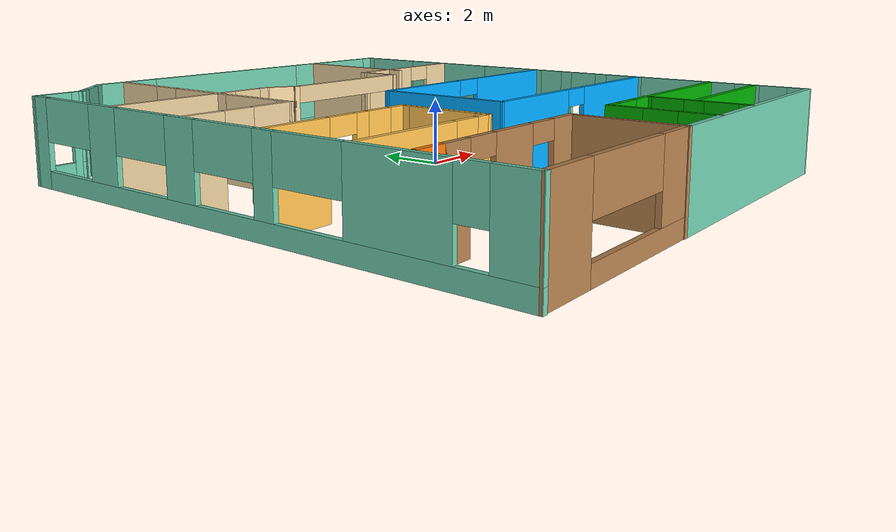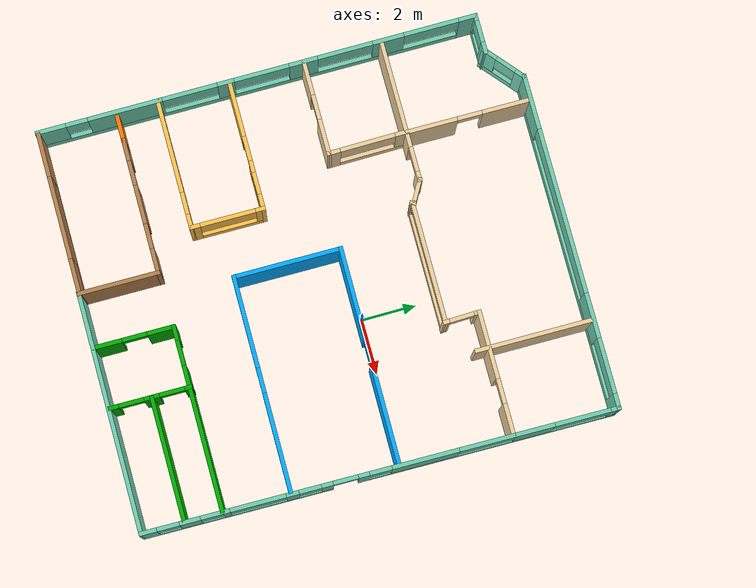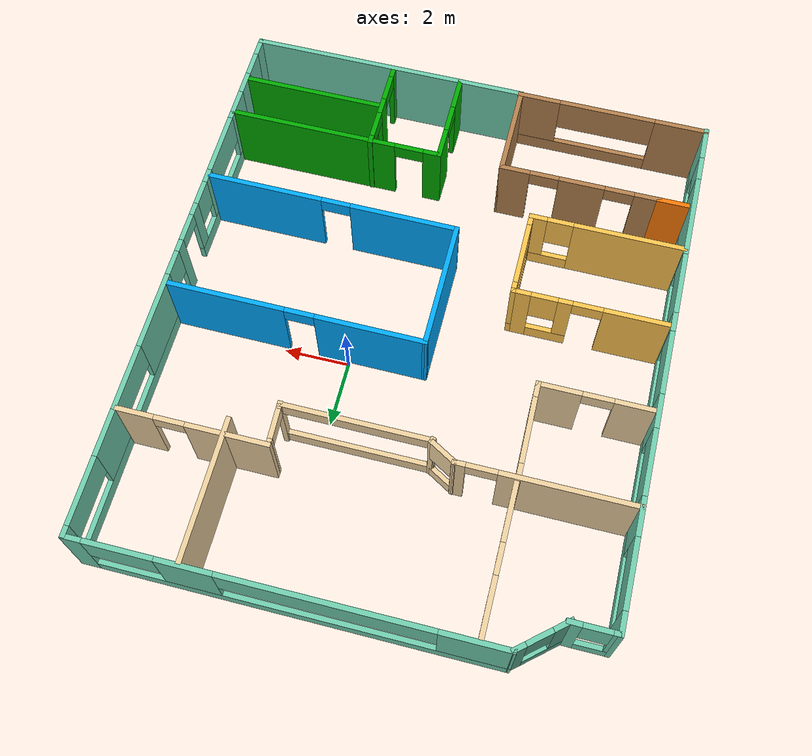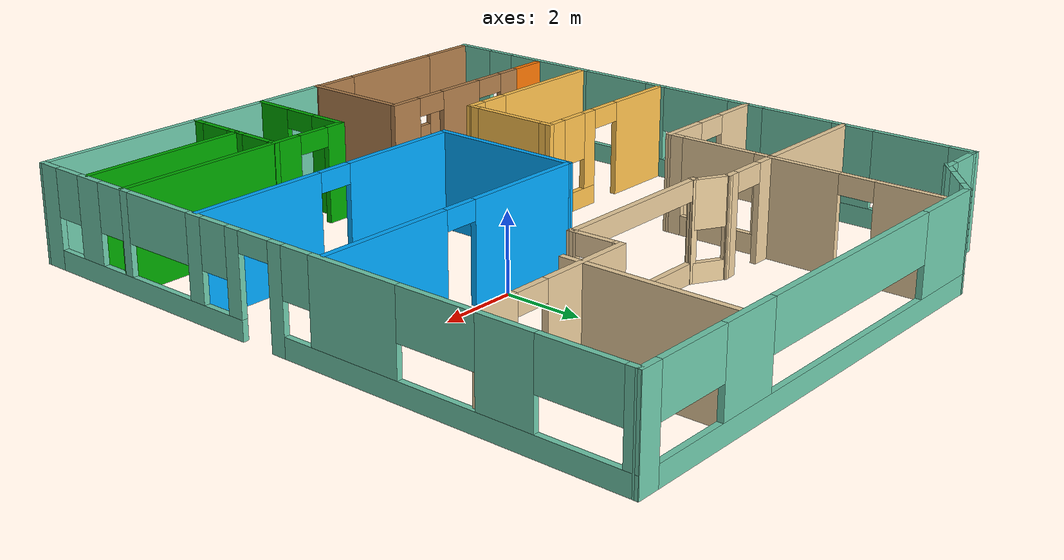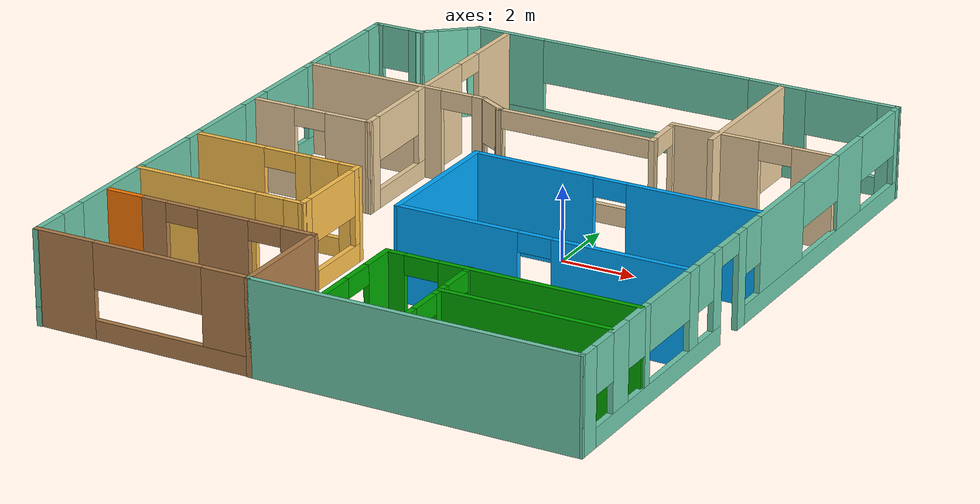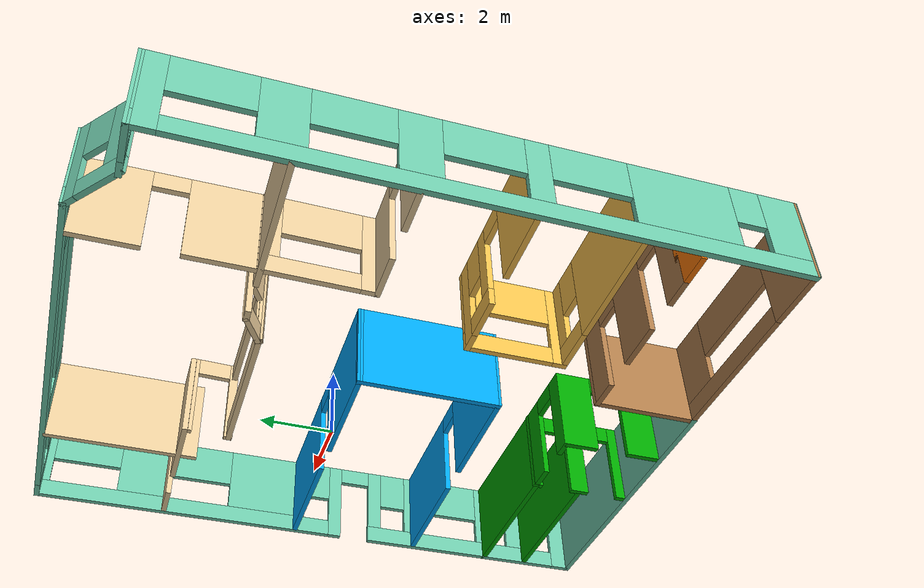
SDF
<?xml version='1.0'?>
<sdf version='1.6'>
  <model name='Building-1'>
    <pose frame=''>-1.79482 -0.843369 0 0 -0 0</pose>
    <link name='Wall_101'>
      <collision name='Wall_101_Collision'>
        <geometry>
          <box>
            <size>1 0.15 2.5</size>
          </box>
        </geometry>
        <pose frame=''>0 0 1.25 0 -0 0</pose>
      </collision>
      <visual name='Wall_101_Visual'>
        <pose frame=''>0 0 1.25 0 -0 0</pose>
        <geometry>
          <box>
            <size>1 0.15 2.5</size>
          </box>
        </geometry>
        <material>
          <script>
            <uri>file://media/materials/scripts/gazebo.material</uri>
            <name>Gazebo/Grey</name>
          </script>
          <ambient>0.996078 0.47451 0.0196078 1</ambient>
        </material>
        <meta>
          <layer>0</layer>
        </meta>
      </visual>
      <pose frame=''>-6.64557 -5.66391 0 0 -0 0</pose>
    </link>
    <link name='Wall_55'>
      <pose frame=''>-3.79556 -5.66391 0 0 -0 0</pose>
      <visual name='Wall_55_Visual_0'>
        <pose frame=''>-2.08336 0 1.25 0 -0 0</pose>
        <geometry>
          <box>
            <size>0.833273 0.15 2.5</size>
          </box>
        </geometry>
        <material>
          <script>
            <uri>file://media/materials/scripts/gazebo.material</uri>
            <name>Gazebo/Wood</name>
          </script>
          <ambient>0.996078 0.47451 0.0196078 1</ambient>
        </material>
        <meta>
          <layer>0</layer>
        </meta>
      </visual>
      <collision name='Wall_55_Collision_0'>
        <geometry>
          <box>
            <size>0.833273 0.15 2.5</size>
          </box>
        </geometry>
        <pose frame=''>-2.08336 0 1.25 0 -0 0</pose>
      </collision>
      <visual name='Wall_55_Visual_1'>
        <pose frame=''>-0.059292 0 1.25 0 -0 0</pose>
        <geometry>
          <box>
            <size>1.41487 0.15 2.5</size>
          </box>
        </geometry>
        <material>
          <script>
            <uri>file://media/materials/scripts/gazebo.material</uri>
            <name>Gazebo/Wood</name>
          </script>
          <ambient>0.996078 0.47451 0.0196078 1</ambient>
        </material>
        <meta>
          <layer>0</layer>
        </meta>
      </visual>
      <collision name='Wall_55_Collision_1'>
        <geometry>
          <box>
            <size>1.41487 0.15 2.5</size>
          </box>
        </geometry>
        <pose frame=''>-0.059292 0 1.25 0 -0 0</pose>
      </collision>
      <visual name='Wall_55_Visual_2'>
        <pose frame=''>2.02407 0 1.25 0 -0 0</pose>
        <geometry>
          <box>
            <size>0.951857 0.15 2.5</size>
          </box>
        </geometry>
        <material>
          <script>
            <uri>file://media/materials/scripts/gazebo.material</uri>
            <name>Gazebo/Wood</name>
          </script>
          <ambient>0.996078 0.47451 0.0196078 1</ambient>
        </material>
        <meta>
          <layer>0</layer>
        </meta>
      </visual>
      <collision name='Wall_55_Collision_2'>
        <geometry>
          <box>
            <size>0.951857 0.15 2.5</size>
          </box>
        </geometry>
        <pose frame=''>2.02407 0 1.25 0 -0 0</pose>
      </collision>
      <visual name='Wall_55_Visual_3'>
        <pose frame=''>-1.21673 0 2.25 0 -0 0</pose>
        <geometry>
          <box>
            <size>0.9 0.15 0.5</size>
          </box>
        </geometry>
        <material>
          <script>
            <uri>file://media/materials/scripts/gazebo.material</uri>
            <name>Gazebo/Wood</name>
          </script>
          <ambient>0.996078 0.47451 0.0196078 1</ambient>
        </material>
        <meta>
          <layer>0</layer>
        </meta>
      </visual>
      <collision name='Wall_55_Collision_3'>
        <geometry>
          <box>
            <size>0.9 0.15 0.5</size>
          </box>
        </geometry>
        <pose frame=''>-1.21673 0 2.25 0 -0 0</pose>
      </collision>
      <visual name='Wall_55_Visual_4'>
        <pose frame=''>1.09814 0 2.25 0 -0 0</pose>
        <geometry>
          <box>
            <size>0.9 0.15 0.5</size>
          </box>
        </geometry>
        <material>
          <script>
            <uri>file://media/materials/scripts/gazebo.material</uri>
            <name>Gazebo/Wood</name>
          </script>
          <ambient>0.996078 0.47451 0.0196078 1</ambient>
        </material>
        <meta>
          <layer>0</layer>
        </meta>
      </visual>
      <collision name='Wall_55_Collision_4'>
        <geometry>
          <box>
            <size>0.9 0.15 0.5</size>
          </box>
        </geometry>
        <pose frame=''>1.09814 0 2.25 0 -0 0</pose>
      </collision>
    </link>
    <link name='Wall_56'>
      <collision name='Wall_56_Collision'>
        <geometry>
          <box>
            <size>3 0.15 2.5</size>
          </box>
        </geometry>
        <pose frame=''>0 0 1.25 0 -0 0</pose>
      </collision>
      <visual name='Wall_56_Visual'>
        <pose frame=''>0 0 1.25 0 -0 0</pose>
        <geometry>
          <box>
            <size>3 0.15 2.5</size>
          </box>
        </geometry>
        <material>
          <script>
            <uri>file://media/materials/scripts/gazebo.material</uri>
            <name>Gazebo/Wood</name>
          </script>
          <ambient>0.996078 0.47451 0.0196078 1</ambient>
        </material>
        <meta>
          <layer>0</layer>
        </meta>
      </visual>
      <pose frame=''>-1.37057 -7.08891 0 0 0 -1.5708</pose>
    </link>
    <link name='Wall_57'>
      <collision name='Wall_57_Collision'>
        <geometry>
          <box>
            <size>8.75 0.15 2.5</size>
          </box>
        </geometry>
        <pose frame=''>0 0 1.25 0 -0 0</pose>
      </collision>
      <visual name='Wall_57_Visual'>
        <pose frame=''>0 0 1.25 0 -0 0</pose>
        <geometry>
          <box>
            <size>8.75 0.15 2.5</size>
          </box>
        </geometry>
        <material>
          <script>
            <uri>file://media/materials/scripts/gazebo.material</uri>
            <name>Gazebo/Grey</name>
          </script>
          <ambient>0.435294 0.796078 0.67451 1</ambient>
        </material>
        <meta>
          <layer>0</layer>
        </meta>
      </visual>
      <pose frame=''>2.92943 -8.51391 0 0 -0 0</pose>
    </link>
    <link name='Wall_58'>
      <pose frame=''>7.27698 -0.015167 0 0 -0 1.5652</pose>
      <visual name='Wall_58_Visual_0'>
        <pose frame=''>-8.25726 0 1.25 0 -0 0</pose>
        <geometry>
          <box>
            <size>0.633232 0.15 2.5</size>
          </box>
        </geometry>
        <material>
          <script>
            <uri>file://media/materials/scripts/gazebo.material</uri>
            <name>Gazebo/Grey</name>
          </script>
          <ambient>0.435294 0.796078 0.67451 1</ambient>
        </material>
        <meta>
          <layer>0</layer>
        </meta>
      </visual>
      <collision name='Wall_58_Collision_0'>
        <geometry>
          <box>
            <size>0.633232 0.15 2.5</size>
          </box>
        </geometry>
        <pose frame=''>-8.25726 0 1.25 0 -0 0</pose>
      </collision>
      <visual name='Wall_58_Visual_1'>
        <pose frame=''>-0.583033 0 1.25 0 -0 0</pose>
        <geometry>
          <box>
            <size>0.396965 0.15 2.5</size>
          </box>
        </geometry>
        <material>
          <script>
            <uri>file://media/materials/scripts/gazebo.material</uri>
            <name>Gazebo/Grey</name>
          </script>
          <ambient>0.435294 0.796078 0.67451 1</ambient>
        </material>
        <meta>
          <layer>0</layer>
        </meta>
      </visual>
      <collision name='Wall_58_Collision_1'>
        <geometry>
          <box>
            <size>0.396965 0.15 2.5</size>
          </box>
        </geometry>
        <pose frame=''>-0.583033 0 1.25 0 -0 0</pose>
      </collision>
      <visual name='Wall_58_Visual_2'>
        <pose frame=''>-4.81108 0 0.25 0 -0 0</pose>
        <geometry>
          <box>
            <size>6.25913 0.15 0.5</size>
          </box>
        </geometry>
        <material>
          <script>
            <uri>file://media/materials/scripts/gazebo.material</uri>
            <name>Gazebo/Grey</name>
          </script>
          <ambient>0.435294 0.796078 0.67451 1</ambient>
        </material>
        <meta>
          <layer>0</layer>
        </meta>
      </visual>
      <collision name='Wall_58_Collision_2'>
        <geometry>
          <box>
            <size>6.25913 0.15 0.5</size>
          </box>
        </geometry>
        <pose frame=''>-4.81108 0 0.25 0 -0 0</pose>
      </collision>
      <visual name='Wall_58_Visual_3'>
        <pose frame=''>4.09466 0 0.25 0 -0 0</pose>
        <geometry>
          <box>
            <size>8.95843 0.15 0.5</size>
          </box>
        </geometry>
        <material>
          <script>
            <uri>file://media/materials/scripts/gazebo.material</uri>
            <name>Gazebo/Grey</name>
          </script>
          <ambient>0.435294 0.796078 0.67451 1</ambient>
        </material>
        <meta>
          <layer>0</layer>
        </meta>
      </visual>
      <collision name='Wall_58_Collision_3'>
        <geometry>
          <box>
            <size>8.95843 0.15 0.5</size>
          </box>
        </geometry>
        <pose frame=''>4.09466 0 0.25 0 -0 0</pose>
      </collision>
      <visual name='Wall_58_Visual_4'>
        <pose frame=''>-6.76763 0 1.5 0 -0 0</pose>
        <geometry>
          <box>
            <size>0.746033 0.15 2</size>
          </box>
        </geometry>
        <material>
          <script>
            <uri>file://media/materials/scripts/gazebo.material</uri>
            <name>Gazebo/Grey</name>
          </script>
          <ambient>0.435294 0.796078 0.67451 1</ambient>
        </material>
        <meta>
          <layer>0</layer>
        </meta>
      </visual>
      <collision name='Wall_58_Collision_4'>
        <geometry>
          <box>
            <size>0.746033 0.15 2</size>
          </box>
        </geometry>
        <pose frame=''>-6.76763 0 1.5 0 -0 0</pose>
      </collision>
      <visual name='Wall_58_Visual_5'>
        <pose frame=''>-5.47131 0 1.5 0 -0 0</pose>
        <geometry>
          <box>
            <size>0.246602 0.15 2</size>
          </box>
        </geometry>
        <material>
          <script>
            <uri>file://media/materials/scripts/gazebo.material</uri>
            <name>Gazebo/Grey</name>
          </script>
          <ambient>0.435294 0.796078 0.67451 1</ambient>
        </material>
        <meta>
          <layer>0</layer>
        </meta>
      </visual>
      <collision name='Wall_58_Collision_5'>
        <geometry>
          <box>
            <size>0.246602 0.15 2</size>
          </box>
        </geometry>
        <pose frame=''>-5.47131 0 1.5 0 -0 0</pose>
      </collision>
      <visual name='Wall_58_Visual_6'>
        <pose frame=''>-3.12103 0 1.5 0 -0 0</pose>
        <geometry>
          <box>
            <size>0.453955 0.15 2</size>
          </box>
        </geometry>
        <material>
          <script>
            <uri>file://media/materials/scripts/gazebo.material</uri>
            <name>Gazebo/Grey</name>
          </script>
          <ambient>0.435294 0.796078 0.67451 1</ambient>
        </material>
        <meta>
          <layer>0</layer>
        </meta>
      </visual>
      <collision name='Wall_58_Collision_6'>
        <geometry>
          <box>
            <size>0.453955 0.15 2</size>
          </box>
        </geometry>
        <pose frame=''>-3.12103 0 1.5 0 -0 0</pose>
      </collision>
      <visual name='Wall_58_Visual_7'>
        <pose frame=''>-1.88778 0 1.5 0 -0 0</pose>
        <geometry>
          <box>
            <size>0.412539 0.15 2</size>
          </box>
        </geometry>
        <material>
          <script>
            <uri>file://media/materials/scripts/gazebo.material</uri>
            <name>Gazebo/Grey</name>
          </script>
          <ambient>0.435294 0.796078 0.67451 1</ambient>
        </material>
        <meta>
          <layer>0</layer>
        </meta>
      </visual>
      <collision name='Wall_58_Collision_7'>
        <geometry>
          <box>
            <size>0.412539 0.15 2</size>
          </box>
        </geometry>
        <pose frame=''>-1.88778 0 1.5 0 -0 0</pose>
      </collision>
      <visual name='Wall_58_Visual_8'>
        <pose frame=''>-1.88778 0 1.5 0 -0 0</pose>
        <geometry>
          <box>
            <size>0.412539 0.15 2</size>
          </box>
        </geometry>
        <material>
          <script>
            <uri>file://media/materials/scripts/gazebo.material</uri>
            <name>Gazebo/Grey</name>
          </script>
          <ambient>0.435294 0.796078 0.67451 1</ambient>
        </material>
        <meta>
          <layer>0</layer>
        </meta>
      </visual>
      <collision name='Wall_58_Collision_8'>
        <geometry>
          <box>
            <size>0.412539 0.15 2</size>
          </box>
        </geometry>
        <pose frame=''>-1.88778 0 1.5 0 -0 0</pose>
      </collision>
      <visual name='Wall_58_Visual_9'>
        <pose frame=''>1.61766 0 1.5 0 -0 0</pose>
        <geometry>
          <box>
            <size>2.40442 0.15 2</size>
          </box>
        </geometry>
        <material>
          <script>
            <uri>file://media/materials/scripts/gazebo.material</uri>
            <name>Gazebo/Grey</name>
          </script>
          <ambient>0.435294 0.796078 0.67451 1</ambient>
        </material>
        <meta>
          <layer>0</layer>
        </meta>
      </visual>
      <collision name='Wall_58_Collision_9'>
        <geometry>
          <box>
            <size>2.40442 0.15 2</size>
          </box>
        </geometry>
        <pose frame=''>1.61766 0 1.5 0 -0 0</pose>
      </collision>
      <visual name='Wall_58_Visual_10'>
        <pose frame=''>5.52613 0 1.5 0 -0 0</pose>
        <geometry>
          <box>
            <size>1.41252 0.15 2</size>
          </box>
        </geometry>
        <material>
          <script>
            <uri>file://media/materials/scripts/gazebo.material</uri>
            <name>Gazebo/Grey</name>
          </script>
          <ambient>0.435294 0.796078 0.67451 1</ambient>
        </material>
        <meta>
          <layer>0</layer>
        </meta>
      </visual>
      <collision name='Wall_58_Collision_10'>
        <geometry>
          <box>
            <size>1.41252 0.15 2</size>
          </box>
        </geometry>
        <pose frame=''>5.52613 0 1.5 0 -0 0</pose>
      </collision>
      <visual name='Wall_58_Visual_11'>
        <pose frame=''>8.40314 0 1.5 0 -0 0</pose>
        <geometry>
          <box>
            <size>0.341482 0.15 2</size>
          </box>
        </geometry>
        <material>
          <script>
            <uri>file://media/materials/scripts/gazebo.material</uri>
            <name>Gazebo/Grey</name>
          </script>
          <ambient>0.435294 0.796078 0.67451 1</ambient>
        </material>
        <meta>
          <layer>0</layer>
        </meta>
      </visual>
      <collision name='Wall_58_Collision_11'>
        <geometry>
          <box>
            <size>0.341482 0.15 2</size>
          </box>
        </geometry>
        <pose frame=''>8.40314 0 1.5 0 -0 0</pose>
      </collision>
      <visual name='Wall_58_Visual_12'>
        <pose frame=''>-7.54064 0 1.9 0 -0 0</pose>
        <geometry>
          <box>
            <size>0.8 0.15 1.2</size>
          </box>
        </geometry>
        <material>
          <script>
            <uri>file://media/materials/scripts/gazebo.material</uri>
            <name>Gazebo/Grey</name>
          </script>
          <ambient>0.435294 0.796078 0.67451 1</ambient>
        </material>
        <meta>
          <layer>0</layer>
        </meta>
      </visual>
      <collision name='Wall_58_Collision_12'>
        <geometry>
          <box>
            <size>0.8 0.15 1.2</size>
          </box>
        </geometry>
        <pose frame=''>-7.54064 0 1.9 0 -0 0</pose>
      </collision>
      <visual name='Wall_58_Visual_13'>
        <pose frame=''>0.01545 0 1.9 0 -0 0</pose>
        <geometry>
          <box>
            <size>0.8 0.15 1.2</size>
          </box>
        </geometry>
        <material>
          <script>
            <uri>file://media/materials/scripts/gazebo.material</uri>
            <name>Gazebo/Grey</name>
          </script>
          <ambient>0.435294 0.796078 0.67451 1</ambient>
        </material>
        <meta>
          <layer>0</layer>
        </meta>
      </visual>
      <collision name='Wall_58_Collision_13'>
        <geometry>
          <box>
            <size>0.8 0.15 1.2</size>
          </box>
        </geometry>
        <pose frame=''>0.01545 0 1.9 0 -0 0</pose>
      </collision>
      <visual name='Wall_58_Visual_14'>
        <pose frame=''>-5.99461 0 1.9 0 -0 0</pose>
        <geometry>
          <box>
            <size>0.8 0.15 1.2</size>
          </box>
        </geometry>
        <material>
          <script>
            <uri>file://media/materials/scripts/gazebo.material</uri>
            <name>Gazebo/Grey</name>
          </script>
          <ambient>0.435294 0.796078 0.67451 1</ambient>
        </material>
        <meta>
          <layer>0</layer>
        </meta>
      </visual>
      <collision name='Wall_58_Collision_14'>
        <geometry>
          <box>
            <size>0.8 0.15 1.2</size>
          </box>
        </geometry>
        <pose frame=''>-5.99461 0 1.9 0 -0 0</pose>
      </collision>
      <visual name='Wall_58_Visual_15'>
        <pose frame=''>-4.34801 0 1.9 0 -0 0</pose>
        <geometry>
          <box>
            <size>2 0.15 1.2</size>
          </box>
        </geometry>
        <material>
          <script>
            <uri>file://media/materials/scripts/gazebo.material</uri>
            <name>Gazebo/Grey</name>
          </script>
          <ambient>0.435294 0.796078 0.67451 1</ambient>
        </material>
        <meta>
          <layer>0</layer>
        </meta>
      </visual>
      <collision name='Wall_58_Collision_15'>
        <geometry>
          <box>
            <size>2 0.15 1.2</size>
          </box>
        </geometry>
        <pose frame=''>-4.34801 0 1.9 0 -0 0</pose>
      </collision>
      <visual name='Wall_58_Visual_16'>
        <pose frame=''>-2.49405 0 1.9 0 -0 0</pose>
        <geometry>
          <box>
            <size>0.8 0.15 1.2</size>
          </box>
        </geometry>
        <material>
          <script>
            <uri>file://media/materials/scripts/gazebo.material</uri>
            <name>Gazebo/Grey</name>
          </script>
          <ambient>0.435294 0.796078 0.67451 1</ambient>
        </material>
        <meta>
          <layer>0</layer>
        </meta>
      </visual>
      <collision name='Wall_58_Collision_16'>
        <geometry>
          <box>
            <size>0.8 0.15 1.2</size>
          </box>
        </geometry>
        <pose frame=''>-2.49405 0 1.9 0 -0 0</pose>
      </collision>
      <visual name='Wall_58_Visual_17'>
        <pose frame=''>3.81987 0 1.9 0 -0 0</pose>
        <geometry>
          <box>
            <size>2 0.15 1.2</size>
          </box>
        </geometry>
        <material>
          <script>
            <uri>file://media/materials/scripts/gazebo.material</uri>
            <name>Gazebo/Grey</name>
          </script>
          <ambient>0.435294 0.796078 0.67451 1</ambient>
        </material>
        <meta>
          <layer>0</layer>
        </meta>
      </visual>
      <collision name='Wall_58_Collision_17'>
        <geometry>
          <box>
            <size>2 0.15 1.2</size>
          </box>
        </geometry>
        <pose frame=''>3.81987 0 1.9 0 -0 0</pose>
      </collision>
      <visual name='Wall_58_Visual_18'>
        <pose frame=''>7.23239 0 1.9 0 -0 0</pose>
        <geometry>
          <box>
            <size>2 0.15 1.2</size>
          </box>
        </geometry>
        <material>
          <script>
            <uri>file://media/materials/scripts/gazebo.material</uri>
            <name>Gazebo/Grey</name>
          </script>
          <ambient>0.435294 0.796078 0.67451 1</ambient>
        </material>
        <meta>
          <layer>0</layer>
        </meta>
      </visual>
      <collision name='Wall_58_Collision_18'>
        <geometry>
          <box>
            <size>2 0.15 1.2</size>
          </box>
        </geometry>
        <pose frame=''>7.23239 0 1.9 0 -0 0</pose>
      </collision>
      <visual name='Wall_58_Visual_19'>
        <pose frame=''>-1.23151 0 2.25 0 -0 0</pose>
        <geometry>
          <box>
            <size>0.9 0.15 0.5</size>
          </box>
        </geometry>
        <material>
          <script>
            <uri>file://media/materials/scripts/gazebo.material</uri>
            <name>Gazebo/Grey</name>
          </script>
          <ambient>0.435294 0.796078 0.67451 1</ambient>
        </material>
        <meta>
          <layer>0</layer>
        </meta>
      </visual>
      <collision name='Wall_58_Collision_19'>
        <geometry>
          <box>
            <size>0.9 0.15 0.5</size>
          </box>
        </geometry>
        <pose frame=''>-1.23151 0 2.25 0 -0 0</pose>
      </collision>
      <visual name='Wall_58_Visual_20'>
        <pose frame=''>-1.23151 0 2.25 0 -0 0</pose>
        <geometry>
          <box>
            <size>0.9 0.15 0.5</size>
          </box>
        </geometry>
        <material>
          <script>
            <uri>file://media/materials/scripts/gazebo.material</uri>
            <name>Gazebo/Grey</name>
          </script>
          <ambient>0.435294 0.796078 0.67451 1</ambient>
        </material>
        <meta>
          <layer>0</layer>
        </meta>
      </visual>
      <collision name='Wall_58_Collision_20'>
        <geometry>
          <box>
            <size>0.9 0.15 0.5</size>
          </box>
        </geometry>
        <pose frame=''>-1.23151 0 2.25 0 -0 0</pose>
      </collision>
    </link>
    <link name='Wall_59'>
      <pose frame=''>1.27452 8.50244 0 0 -0 3.14159</pose>
      <visual name='Wall_59_Visual_0'>
        <pose frame=''>-5.83178 0 1.25 0 -0 0</pose>
        <geometry>
          <box>
            <size>0.586429 0.15 2.5</size>
          </box>
        </geometry>
        <material>
          <script>
            <uri>file://media/materials/scripts/gazebo.material</uri>
            <name>Gazebo/Grey</name>
          </script>
          <ambient>0.435294 0.796078 0.67451 1</ambient>
        </material>
        <meta>
          <layer>0</layer>
        </meta>
      </visual>
      <collision name='Wall_59_Collision_0'>
        <geometry>
          <box>
            <size>0.586429 0.15 2.5</size>
          </box>
        </geometry>
        <pose frame=''>-5.83178 0 1.25 0 -0 0</pose>
      </collision>
      <visual name='Wall_59_Visual_1'>
        <pose frame=''>0.293215 0 0.25 0 -0 0</pose>
        <geometry>
          <box>
            <size>11.6636 0.15 0.5</size>
          </box>
        </geometry>
        <material>
          <script>
            <uri>file://media/materials/scripts/gazebo.material</uri>
            <name>Gazebo/Grey</name>
          </script>
          <ambient>0.435294 0.796078 0.67451 1</ambient>
        </material>
        <meta>
          <layer>0</layer>
        </meta>
      </visual>
      <collision name='Wall_59_Collision_1'>
        <geometry>
          <box>
            <size>11.6636 0.15 0.5</size>
          </box>
        </geometry>
        <pose frame=''>0.293215 0 0.25 0 -0 0</pose>
      </collision>
      <visual name='Wall_59_Visual_2'>
        <pose frame=''>-2.72513 0 1.5 0 -0 0</pose>
        <geometry>
          <box>
            <size>1.62688 0.15 2</size>
          </box>
        </geometry>
        <material>
          <script>
            <uri>file://media/materials/scripts/gazebo.material</uri>
            <name>Gazebo/Grey</name>
          </script>
          <ambient>0.435294 0.796078 0.67451 1</ambient>
        </material>
        <meta>
          <layer>0</layer>
        </meta>
      </visual>
      <collision name='Wall_59_Collision_2'>
        <geometry>
          <box>
            <size>1.62688 0.15 2</size>
          </box>
        </geometry>
        <pose frame=''>-2.72513 0 1.5 0 -0 0</pose>
      </collision>
      <visual name='Wall_59_Visual_3'>
        <pose frame=''>5.10665 0 1.5 0 -0 0</pose>
        <geometry>
          <box>
            <size>2.03669 0.15 2</size>
          </box>
        </geometry>
        <material>
          <script>
            <uri>file://media/materials/scripts/gazebo.material</uri>
            <name>Gazebo/Grey</name>
          </script>
          <ambient>0.435294 0.796078 0.67451 1</ambient>
        </material>
        <meta>
          <layer>0</layer>
        </meta>
      </visual>
      <collision name='Wall_59_Collision_3'>
        <geometry>
          <box>
            <size>2.03669 0.15 2</size>
          </box>
        </geometry>
        <pose frame=''>5.10665 0 1.5 0 -0 0</pose>
      </collision>
      <visual name='Wall_59_Visual_4'>
        <pose frame=''>-4.53857 0 1.9 0 -0 0</pose>
        <geometry>
          <box>
            <size>2 0.15 1.2</size>
          </box>
        </geometry>
        <material>
          <script>
            <uri>file://media/materials/scripts/gazebo.material</uri>
            <name>Gazebo/Grey</name>
          </script>
          <ambient>0.435294 0.796078 0.67451 1</ambient>
        </material>
        <meta>
          <layer>0</layer>
        </meta>
      </visual>
      <collision name='Wall_59_Collision_4'>
        <geometry>
          <box>
            <size>2 0.15 1.2</size>
          </box>
        </geometry>
        <pose frame=''>-4.53857 0 1.9 0 -0 0</pose>
      </collision>
      <visual name='Wall_59_Visual_5'>
        <pose frame=''>1.08831 0 1.9 0 -0 0</pose>
        <geometry>
          <box>
            <size>6 0.15 1.2</size>
          </box>
        </geometry>
        <material>
          <script>
            <uri>file://media/materials/scripts/gazebo.material</uri>
            <name>Gazebo/Grey</name>
          </script>
          <ambient>0.435294 0.796078 0.67451 1</ambient>
        </material>
        <meta>
          <layer>0</layer>
        </meta>
      </visual>
      <collision name='Wall_59_Collision_5'>
        <geometry>
          <box>
            <size>6 0.15 1.2</size>
          </box>
        </geometry>
        <pose frame=''>1.08831 0 1.9 0 -0 0</pose>
      </collision>
    </link>
    <link name='Wall_60'>
      <pose frame=''>-5.41275 7.93742 0 0 0 -2.43304</pose>
      <visual name='Wall_60_Visual_0'>
        <pose frame=''>-0.703208 0 1.25 0 -0 0</pose>
        <geometry>
          <box>
            <size>0.422171 0.15 2.5</size>
          </box>
        </geometry>
        <material>
          <script>
            <uri>file://media/materials/scripts/gazebo.material</uri>
            <name>Gazebo/Grey</name>
          </script>
          <ambient>0.435294 0.796078 0.67451 1</ambient>
        </material>
        <meta>
          <layer>0</layer>
        </meta>
      </visual>
      <collision name='Wall_60_Collision_0'>
        <geometry>
          <box>
            <size>0.422171 0.15 2.5</size>
          </box>
        </geometry>
        <pose frame=''>-0.703208 0 1.25 0 -0 0</pose>
      </collision>
      <visual name='Wall_60_Visual_1'>
        <pose frame=''>0.211086 0 0.25 0 -0 0</pose>
        <geometry>
          <box>
            <size>1.40642 0.15 0.5</size>
          </box>
        </geometry>
        <material>
          <script>
            <uri>file://media/materials/scripts/gazebo.material</uri>
            <name>Gazebo/Grey</name>
          </script>
          <ambient>0.435294 0.796078 0.67451 1</ambient>
        </material>
        <meta>
          <layer>0</layer>
        </meta>
      </visual>
      <collision name='Wall_60_Collision_1'>
        <geometry>
          <box>
            <size>1.40642 0.15 0.5</size>
          </box>
        </geometry>
        <pose frame=''>0.211086 0 0.25 0 -0 0</pose>
      </collision>
      <visual name='Wall_60_Visual_2'>
        <pose frame=''>0.611086 0 1.5 0 -0 0</pose>
        <geometry>
          <box>
            <size>0.606416 0.15 2</size>
          </box>
        </geometry>
        <material>
          <script>
            <uri>file://media/materials/scripts/gazebo.material</uri>
            <name>Gazebo/Grey</name>
          </script>
          <ambient>0.435294 0.796078 0.67451 1</ambient>
        </material>
        <meta>
          <layer>0</layer>
        </meta>
      </visual>
      <collision name='Wall_60_Collision_2'>
        <geometry>
          <box>
            <size>0.606416 0.15 2</size>
          </box>
        </geometry>
        <pose frame=''>0.611086 0 1.5 0 -0 0</pose>
      </collision>
      <visual name='Wall_60_Visual_3'>
        <pose frame=''>-0.092122 0 1.9 0 -0 0</pose>
        <geometry>
          <box>
            <size>0.8 0.15 1.2</size>
          </box>
        </geometry>
        <material>
          <script>
            <uri>file://media/materials/scripts/gazebo.material</uri>
            <name>Gazebo/Grey</name>
          </script>
          <ambient>0.435294 0.796078 0.67451 1</ambient>
        </material>
        <meta>
          <layer>0</layer>
        </meta>
      </visual>
      <collision name='Wall_60_Collision_3'>
        <geometry>
          <box>
            <size>0.8 0.15 1.2</size>
          </box>
        </geometry>
        <pose frame=''>-0.092122 0 1.9 0 -0 0</pose>
      </collision>
    </link>
    <link name='Wall_65'>
      <pose frame=''>-6.64959 7.42898 0 0 -0 3.14159</pose>
      <visual name='Wall_65_Visual_0'>
        <pose frame=''>-0.53233 0 1.25 0 -0 0</pose>
        <geometry>
          <box>
            <size>0.43534 0.15 2.5</size>
          </box>
        </geometry>
        <material>
          <script>
            <uri>file://media/materials/scripts/gazebo.material</uri>
            <name>Gazebo/Grey</name>
          </script>
          <ambient>0.435294 0.796078 0.67451 1</ambient>
        </material>
        <meta>
          <layer>0</layer>
        </meta>
      </visual>
      <collision name='Wall_65_Collision_0'>
        <geometry>
          <box>
            <size>0.43534 0.15 2.5</size>
          </box>
        </geometry>
        <pose frame=''>-0.53233 0 1.25 0 -0 0</pose>
      </collision>
      <visual name='Wall_65_Visual_1'>
        <pose frame=''>0.21767 0 0.25 0 -0 0</pose>
        <geometry>
          <box>
            <size>1.06466 0.15 0.5</size>
          </box>
        </geometry>
        <material>
          <script>
            <uri>file://media/materials/scripts/gazebo.material</uri>
            <name>Gazebo/Grey</name>
          </script>
          <ambient>0.435294 0.796078 0.67451 1</ambient>
        </material>
        <meta>
          <layer>0</layer>
        </meta>
      </visual>
      <collision name='Wall_65_Collision_1'>
        <geometry>
          <box>
            <size>1.06466 0.15 0.5</size>
          </box>
        </geometry>
        <pose frame=''>0.21767 0 0.25 0 -0 0</pose>
      </collision>
      <visual name='Wall_65_Visual_2'>
        <pose frame=''>0.61767 0 1.5 0 -0 0</pose>
        <geometry>
          <box>
            <size>0.26466 0.15 2</size>
          </box>
        </geometry>
        <material>
          <script>
            <uri>file://media/materials/scripts/gazebo.material</uri>
            <name>Gazebo/Grey</name>
          </script>
          <ambient>0.435294 0.796078 0.67451 1</ambient>
        </material>
        <meta>
          <layer>0</layer>
        </meta>
      </visual>
      <collision name='Wall_65_Collision_2'>
        <geometry>
          <box>
            <size>0.26466 0.15 2</size>
          </box>
        </geometry>
        <pose frame=''>0.61767 0 1.5 0 -0 0</pose>
      </collision>
      <visual name='Wall_65_Visual_3'>
        <pose frame=''>0.08534 0 1.9 0 -0 0</pose>
        <geometry>
          <box>
            <size>0.8 0.15 1.2</size>
          </box>
        </geometry>
        <material>
          <script>
            <uri>file://media/materials/scripts/gazebo.material</uri>
            <name>Gazebo/Grey</name>
          </script>
          <ambient>0.435294 0.796078 0.67451 1</ambient>
        </material>
        <meta>
          <layer>0</layer>
        </meta>
      </visual>
      <collision name='Wall_65_Collision_3'>
        <geometry>
          <box>
            <size>0.8 0.15 1.2</size>
          </box>
        </geometry>
        <pose frame=''>0.08534 0 1.9 0 -0 0</pose>
      </collision>
    </link>
    <link name='Wall_66'>
      <pose frame=''>-7.28687 -0.542232 0 0 0 -1.56606</pose>
      <visual name='Wall_66_Visual_0'>
        <pose frame=''>-7.70025 0 1.25 0 -0 0</pose>
        <geometry>
          <box>
            <size>0.692866 0.15 2.5</size>
          </box>
        </geometry>
        <material>
          <script>
            <uri>file://media/materials/scripts/gazebo.material</uri>
            <name>Gazebo/Grey</name>
          </script>
          <ambient>0.435294 0.796078 0.67451 1</ambient>
        </material>
        <meta>
          <layer>0</layer>
        </meta>
      </visual>
      <collision name='Wall_66_Collision_0'>
        <geometry>
          <box>
            <size>0.692866 0.15 2.5</size>
          </box>
        </geometry>
        <pose frame=''>-7.70025 0 1.25 0 -0 0</pose>
      </collision>
      <visual name='Wall_66_Visual_1'>
        <pose frame=''>0.346433 0 0.25 0 -0 0</pose>
        <geometry>
          <box>
            <size>15.4005 0.15 0.5</size>
          </box>
        </geometry>
        <material>
          <script>
            <uri>file://media/materials/scripts/gazebo.material</uri>
            <name>Gazebo/Grey</name>
          </script>
          <ambient>0.435294 0.796078 0.67451 1</ambient>
        </material>
        <meta>
          <layer>0</layer>
        </meta>
      </visual>
      <collision name='Wall_66_Collision_1'>
        <geometry>
          <box>
            <size>15.4005 0.15 0.5</size>
          </box>
        </geometry>
        <pose frame=''>0.346433 0 0.25 0 -0 0</pose>
      </collision>
      <visual name='Wall_66_Visual_2'>
        <pose frame=''>-4.78225 0 1.5 0 -0 0</pose>
        <geometry>
          <box>
            <size>1.14314 0.15 2</size>
          </box>
        </geometry>
        <material>
          <script>
            <uri>file://media/materials/scripts/gazebo.material</uri>
            <name>Gazebo/Grey</name>
          </script>
          <ambient>0.435294 0.796078 0.67451 1</ambient>
        </material>
        <meta>
          <layer>0</layer>
        </meta>
      </visual>
      <collision name='Wall_66_Collision_2'>
        <geometry>
          <box>
            <size>1.14314 0.15 2</size>
          </box>
        </geometry>
        <pose frame=''>-4.78225 0 1.5 0 -0 0</pose>
      </collision>
      <visual name='Wall_66_Visual_3'>
        <pose frame=''>-1.6864 0 1.5 0 -0 0</pose>
        <geometry>
          <box>
            <size>1.04855 0.15 2</size>
          </box>
        </geometry>
        <material>
          <script>
            <uri>file://media/materials/scripts/gazebo.material</uri>
            <name>Gazebo/Grey</name>
          </script>
          <ambient>0.435294 0.796078 0.67451 1</ambient>
        </material>
        <meta>
          <layer>0</layer>
        </meta>
      </visual>
      <collision name='Wall_66_Collision_3'>
        <geometry>
          <box>
            <size>1.04855 0.15 2</size>
          </box>
        </geometry>
        <pose frame=''>-1.6864 0 1.5 0 -0 0</pose>
      </collision>
      <visual name='Wall_66_Visual_4'>
        <pose frame=''>1.14316 0 1.5 0 -0 0</pose>
        <geometry>
          <box>
            <size>0.610584 0.15 2</size>
          </box>
        </geometry>
        <material>
          <script>
            <uri>file://media/materials/scripts/gazebo.material</uri>
            <name>Gazebo/Grey</name>
          </script>
          <ambient>0.435294 0.796078 0.67451 1</ambient>
        </material>
        <meta>
          <layer>0</layer>
        </meta>
      </visual>
      <collision name='Wall_66_Collision_4'>
        <geometry>
          <box>
            <size>0.610584 0.15 2</size>
          </box>
        </geometry>
        <pose frame=''>1.14316 0 1.5 0 -0 0</pose>
      </collision>
      <visual name='Wall_66_Visual_5'>
        <pose frame=''>4.7972 0 1.5 0 -0 0</pose>
        <geometry>
          <box>
            <size>2.6975 0.15 2</size>
          </box>
        </geometry>
        <material>
          <script>
            <uri>file://media/materials/scripts/gazebo.material</uri>
            <name>Gazebo/Grey</name>
          </script>
          <ambient>0.435294 0.796078 0.67451 1</ambient>
        </material>
        <meta>
          <layer>0</layer>
        </meta>
      </visual>
      <collision name='Wall_66_Collision_5'>
        <geometry>
          <box>
            <size>2.6975 0.15 2</size>
          </box>
        </geometry>
        <pose frame=''>4.7972 0 1.5 0 -0 0</pose>
      </collision>
      <visual name='Wall_66_Visual_6'>
        <pose frame=''>7.49632 0 1.5 0 -0 0</pose>
        <geometry>
          <box>
            <size>1.10073 0.15 2</size>
          </box>
        </geometry>
        <material>
          <script>
            <uri>file://media/materials/scripts/gazebo.material</uri>
            <name>Gazebo/Grey</name>
          </script>
          <ambient>0.435294 0.796078 0.67451 1</ambient>
        </material>
        <meta>
          <layer>0</layer>
        </meta>
      </visual>
      <collision name='Wall_66_Collision_6'>
        <geometry>
          <box>
            <size>1.10073 0.15 2</size>
          </box>
        </geometry>
        <pose frame=''>7.49632 0 1.5 0 -0 0</pose>
      </collision>
      <visual name='Wall_66_Visual_7'>
        <pose frame=''>-6.35382 0 1.9 0 -0 0</pose>
        <geometry>
          <box>
            <size>2 0.15 1.2</size>
          </box>
        </geometry>
        <material>
          <script>
            <uri>file://media/materials/scripts/gazebo.material</uri>
            <name>Gazebo/Grey</name>
          </script>
          <ambient>0.435294 0.796078 0.67451 1</ambient>
        </material>
        <meta>
          <layer>0</layer>
        </meta>
      </visual>
      <collision name='Wall_66_Collision_7'>
        <geometry>
          <box>
            <size>2 0.15 1.2</size>
          </box>
        </geometry>
        <pose frame=''>-6.35382 0 1.9 0 -0 0</pose>
      </collision>
      <visual name='Wall_66_Visual_8'>
        <pose frame=''>-3.21068 0 1.9 0 -0 0</pose>
        <geometry>
          <box>
            <size>2 0.15 1.2</size>
          </box>
        </geometry>
        <material>
          <script>
            <uri>file://media/materials/scripts/gazebo.material</uri>
            <name>Gazebo/Grey</name>
          </script>
          <ambient>0.435294 0.796078 0.67451 1</ambient>
        </material>
        <meta>
          <layer>0</layer>
        </meta>
      </visual>
      <collision name='Wall_66_Collision_8'>
        <geometry>
          <box>
            <size>2 0.15 1.2</size>
          </box>
        </geometry>
        <pose frame=''>-3.21068 0 1.9 0 -0 0</pose>
      </collision>
      <visual name='Wall_66_Visual_9'>
        <pose frame=''>-0.162128 0 1.9 0 -0 0</pose>
        <geometry>
          <box>
            <size>2 0.15 1.2</size>
          </box>
        </geometry>
        <material>
          <script>
            <uri>file://media/materials/scripts/gazebo.material</uri>
            <name>Gazebo/Grey</name>
          </script>
          <ambient>0.435294 0.796078 0.67451 1</ambient>
        </material>
        <meta>
          <layer>0</layer>
        </meta>
      </visual>
      <collision name='Wall_66_Collision_9'>
        <geometry>
          <box>
            <size>2 0.15 1.2</size>
          </box>
        </geometry>
        <pose frame=''>-0.162128 0 1.9 0 -0 0</pose>
      </collision>
      <visual name='Wall_66_Visual_10'>
        <pose frame=''>2.44846 0 1.9 0 -0 0</pose>
        <geometry>
          <box>
            <size>2 0.15 1.2</size>
          </box>
        </geometry>
        <material>
          <script>
            <uri>file://media/materials/scripts/gazebo.material</uri>
            <name>Gazebo/Grey</name>
          </script>
          <ambient>0.435294 0.796078 0.67451 1</ambient>
        </material>
        <meta>
          <layer>0</layer>
        </meta>
      </visual>
      <collision name='Wall_66_Collision_10'>
        <geometry>
          <box>
            <size>2 0.15 1.2</size>
          </box>
        </geometry>
        <pose frame=''>2.44846 0 1.9 0 -0 0</pose>
      </collision>
      <visual name='Wall_66_Visual_11'>
        <pose frame=''>6.54595 0 1.9 0 -0 0</pose>
        <geometry>
          <box>
            <size>0.8 0.15 1.2</size>
          </box>
        </geometry>
        <material>
          <script>
            <uri>file://media/materials/scripts/gazebo.material</uri>
            <name>Gazebo/Grey</name>
          </script>
          <ambient>0.435294 0.796078 0.67451 1</ambient>
        </material>
        <meta>
          <layer>0</layer>
        </meta>
      </visual>
      <collision name='Wall_66_Collision_11'>
        <geometry>
          <box>
            <size>0.8 0.15 1.2</size>
          </box>
        </geometry>
        <pose frame=''>6.54595 0 1.9 0 -0 0</pose>
      </collision>
    </link>
    <link name='Wall_67'>
      <pose frame=''>-4.30246 -8.49175 0 0 -0 0</pose>
      <visual name='Wall_67_Visual_0'>
        <pose frame=''>-2.17925 0 1.25 0 -0 0</pose>
        <geometry>
          <box>
            <size>1.68488 0.15 2.5</size>
          </box>
        </geometry>
        <material>
          <script>
            <uri>file://media/materials/scripts/gazebo.material</uri>
            <name>Gazebo/Wood</name>
          </script>
          <ambient>0.435294 0.796078 0.67451 1</ambient>
        </material>
        <meta>
          <layer>0</layer>
        </meta>
      </visual>
      <collision name='Wall_67_Collision_0'>
        <geometry>
          <box>
            <size>1.68488 0.15 2.5</size>
          </box>
        </geometry>
        <pose frame=''>-2.17925 0 1.25 0 -0 0</pose>
      </collision>
      <visual name='Wall_67_Visual_1'>
        <pose frame=''>0.842439 0 0.25 0 -0 0</pose>
        <geometry>
          <box>
            <size>4.3585 0.15 0.5</size>
          </box>
        </geometry>
        <material>
          <script>
            <uri>file://media/materials/scripts/gazebo.material</uri>
            <name>Gazebo/Wood</name>
          </script>
          <ambient>0.435294 0.796078 0.67451 1</ambient>
        </material>
        <meta>
          <layer>0</layer>
        </meta>
      </visual>
      <collision name='Wall_67_Collision_1'>
        <geometry>
          <box>
            <size>4.3585 0.15 0.5</size>
          </box>
        </geometry>
        <pose frame=''>0.842439 0 0.25 0 -0 0</pose>
      </collision>
      <visual name='Wall_67_Visual_2'>
        <pose frame=''>2.34244 0 1.5 0 -0 0</pose>
        <geometry>
          <box>
            <size>1.3585 0.15 2</size>
          </box>
        </geometry>
        <material>
          <script>
            <uri>file://media/materials/scripts/gazebo.material</uri>
            <name>Gazebo/Wood</name>
          </script>
          <ambient>0.435294 0.796078 0.67451 1</ambient>
        </material>
        <meta>
          <layer>0</layer>
        </meta>
      </visual>
      <collision name='Wall_67_Collision_2'>
        <geometry>
          <box>
            <size>1.3585 0.15 2</size>
          </box>
        </geometry>
        <pose frame=''>2.34244 0 1.5 0 -0 0</pose>
      </collision>
      <visual name='Wall_67_Visual_3'>
        <pose frame=''>0.163188 0 1.9 0 -0 0</pose>
        <geometry>
          <box>
            <size>3 0.15 1.2</size>
          </box>
        </geometry>
        <material>
          <script>
            <uri>file://media/materials/scripts/gazebo.material</uri>
            <name>Gazebo/Wood</name>
          </script>
          <ambient>0.435294 0.796078 0.67451 1</ambient>
        </material>
        <meta>
          <layer>0</layer>
        </meta>
      </visual>
      <collision name='Wall_67_Collision_3'>
        <geometry>
          <box>
            <size>3 0.15 1.2</size>
          </box>
        </geometry>
        <pose frame=''>0.163188 0 1.9 0 -0 0</pose>
      </collision>
    </link>
    <link name='Wall_71'>
      <pose frame=''>-4.91996 -4.15514 0 0 0 -6.7e-05</pose>
      <visual name='Wall_71_Visual_0'>
        <pose frame=''>-0.681713 0 1.25 0 -0 0</pose>
        <geometry>
          <box>
            <size>3.41204 0.15 2.5</size>
          </box>
        </geometry>
        <material>
          <script>
            <uri>file://media/materials/scripts/gazebo.material</uri>
            <name>Gazebo/Grey</name>
          </script>
          <ambient>1 0.764706 0.305882 1</ambient>
        </material>
        <meta>
          <layer>0</layer>
        </meta>
      </visual>
      <collision name='Wall_71_Collision_0'>
        <geometry>
          <box>
            <size>3.41204 0.15 2.5</size>
          </box>
        </geometry>
        <pose frame=''>-0.681713 0 1.25 0 -0 0</pose>
      </collision>
      <visual name='Wall_71_Visual_1'>
        <pose frame=''>1.70602 0 0.25 0 -0 0</pose>
        <geometry>
          <box>
            <size>1.36343 0.15 0.5</size>
          </box>
        </geometry>
        <material>
          <script>
            <uri>file://media/materials/scripts/gazebo.material</uri>
            <name>Gazebo/Grey</name>
          </script>
          <ambient>1 0.764706 0.305882 1</ambient>
        </material>
        <meta>
          <layer>0</layer>
        </meta>
      </visual>
      <collision name='Wall_71_Collision_1'>
        <geometry>
          <box>
            <size>1.36343 0.15 0.5</size>
          </box>
        </geometry>
        <pose frame=''>1.70602 0 0.25 0 -0 0</pose>
      </collision>
      <visual name='Wall_71_Visual_2'>
        <pose frame=''>2.10602 0 1.5 0 -0 0</pose>
        <geometry>
          <box>
            <size>0.563425 0.15 2</size>
          </box>
        </geometry>
        <material>
          <script>
            <uri>file://media/materials/scripts/gazebo.material</uri>
            <name>Gazebo/Grey</name>
          </script>
          <ambient>1 0.764706 0.305882 1</ambient>
        </material>
        <meta>
          <layer>0</layer>
        </meta>
      </visual>
      <collision name='Wall_71_Collision_2'>
        <geometry>
          <box>
            <size>0.563425 0.15 2</size>
          </box>
        </geometry>
        <pose frame=''>2.10602 0 1.5 0 -0 0</pose>
      </collision>
      <visual name='Wall_71_Visual_3'>
        <pose frame=''>1.42431 0 1.9 0 -0 0</pose>
        <geometry>
          <box>
            <size>0.8 0.15 1.2</size>
          </box>
        </geometry>
        <material>
          <script>
            <uri>file://media/materials/scripts/gazebo.material</uri>
            <name>Gazebo/Grey</name>
          </script>
          <ambient>1 0.764706 0.305882 1</ambient>
        </material>
        <meta>
          <layer>0</layer>
        </meta>
      </visual>
      <collision name='Wall_71_Collision_3'>
        <geometry>
          <box>
            <size>0.8 0.15 1.2</size>
          </box>
        </geometry>
        <pose frame=''>1.42431 0 1.9 0 -0 0</pose>
      </collision>
    </link>
    <link name='Wall_72'>
      <pose frame=''>-2.60723 -2.8553 0 0 -0 1.5708</pose>
      <visual name='Wall_72_Visual_0'>
        <pose frame=''>-1.17814 0 1.25 0 -0 0</pose>
        <geometry>
          <box>
            <size>0.393718 0.15 2.5</size>
          </box>
        </geometry>
        <material>
          <script>
            <uri>file://media/materials/scripts/gazebo.material</uri>
            <name>Gazebo/Grey</name>
          </script>
          <ambient>1 0.764706 0.305882 1</ambient>
        </material>
        <meta>
          <layer>0</layer>
        </meta>
      </visual>
      <collision name='Wall_72_Collision_0'>
        <geometry>
          <box>
            <size>0.393718 0.15 2.5</size>
          </box>
        </geometry>
        <pose frame=''>-1.17814 0 1.25 0 -0 0</pose>
      </collision>
      <visual name='Wall_72_Visual_1'>
        <pose frame=''>0.196859 0 0.25 0 -0 0</pose>
        <geometry>
          <box>
            <size>2.35628 0.15 0.5</size>
          </box>
        </geometry>
        <material>
          <script>
            <uri>file://media/materials/scripts/gazebo.material</uri>
            <name>Gazebo/Grey</name>
          </script>
          <ambient>1 0.764706 0.305882 1</ambient>
        </material>
        <meta>
          <layer>0</layer>
        </meta>
      </visual>
      <collision name='Wall_72_Collision_1'>
        <geometry>
          <box>
            <size>2.35628 0.15 0.5</size>
          </box>
        </geometry>
        <pose frame=''>0.196859 0 0.25 0 -0 0</pose>
      </collision>
      <visual name='Wall_72_Visual_2'>
        <pose frame=''>1.19686 0 1.5 0 -0 0</pose>
        <geometry>
          <box>
            <size>0.356282 0.15 2</size>
          </box>
        </geometry>
        <material>
          <script>
            <uri>file://media/materials/scripts/gazebo.material</uri>
            <name>Gazebo/Grey</name>
          </script>
          <ambient>1 0.764706 0.305882 1</ambient>
        </material>
        <meta>
          <layer>0</layer>
        </meta>
      </visual>
      <collision name='Wall_72_Collision_2'>
        <geometry>
          <box>
            <size>0.356282 0.15 2</size>
          </box>
        </geometry>
        <pose frame=''>1.19686 0 1.5 0 -0 0</pose>
      </collision>
      <visual name='Wall_72_Visual_3'>
        <pose frame=''>0.018718 0 1.9 0 -0 0</pose>
        <geometry>
          <box>
            <size>2 0.15 1.2</size>
          </box>
        </geometry>
        <material>
          <script>
            <uri>file://media/materials/scripts/gazebo.material</uri>
            <name>Gazebo/Grey</name>
          </script>
          <ambient>1 0.764706 0.305882 1</ambient>
        </material>
        <meta>
          <layer>0</layer>
        </meta>
      </visual>
      <collision name='Wall_72_Collision_3'>
        <geometry>
          <box>
            <size>2 0.15 1.2</size>
          </box>
        </geometry>
        <pose frame=''>0.018718 0 1.9 0 -0 0</pose>
      </collision>
    </link>
    <link name='Wall_73'>
      <pose frame=''>-4.90723 -1.5553 0 0 -0 3.14159</pose>
      <visual name='Wall_73_Visual_0'>
        <pose frame=''>-2.07496 0 1.25 0 -0 0</pose>
        <geometry>
          <box>
            <size>0.600078 0.15 2.5</size>
          </box>
        </geometry>
        <material>
          <script>
            <uri>file://media/materials/scripts/gazebo.material</uri>
            <name>Gazebo/Grey</name>
          </script>
          <ambient>1 0.764706 0.305882 1</ambient>
        </material>
        <meta>
          <layer>0</layer>
        </meta>
      </visual>
      <collision name='Wall_73_Collision_0'>
        <geometry>
          <box>
            <size>0.600078 0.15 2.5</size>
          </box>
        </geometry>
        <pose frame=''>-2.07496 0 1.25 0 -0 0</pose>
      </collision>
      <visual name='Wall_73_Visual_1'>
        <pose frame=''>1.36329 0 1.25 0 -0 0</pose>
        <geometry>
          <box>
            <size>2.02342 0.15 2.5</size>
          </box>
        </geometry>
        <material>
          <script>
            <uri>file://media/materials/scripts/gazebo.material</uri>
            <name>Gazebo/Grey</name>
          </script>
          <ambient>1 0.764706 0.305882 1</ambient>
        </material>
        <meta>
          <layer>0</layer>
        </meta>
      </visual>
      <collision name='Wall_73_Collision_1'>
        <geometry>
          <box>
            <size>2.02342 0.15 2.5</size>
          </box>
        </geometry>
        <pose frame=''>1.36329 0 1.25 0 -0 0</pose>
      </collision>
      <visual name='Wall_73_Visual_2'>
        <pose frame=''>-1.16167 0 0.25 0 -0 0</pose>
        <geometry>
          <box>
            <size>1.2265 0.15 0.5</size>
          </box>
        </geometry>
        <material>
          <script>
            <uri>file://media/materials/scripts/gazebo.material</uri>
            <name>Gazebo/Grey</name>
          </script>
          <ambient>1 0.764706 0.305882 1</ambient>
        </material>
        <meta>
          <layer>0</layer>
        </meta>
      </visual>
      <collision name='Wall_73_Collision_2'>
        <geometry>
          <box>
            <size>1.2265 0.15 0.5</size>
          </box>
        </geometry>
        <pose frame=''>-1.16167 0 0.25 0 -0 0</pose>
      </collision>
      <visual name='Wall_73_Visual_3'>
        <pose frame=''>-0.761671 0 1.5 0 -0 0</pose>
        <geometry>
          <box>
            <size>0.426503 0.15 2</size>
          </box>
        </geometry>
        <material>
          <script>
            <uri>file://media/materials/scripts/gazebo.material</uri>
            <name>Gazebo/Grey</name>
          </script>
          <ambient>1 0.764706 0.305882 1</ambient>
        </material>
        <meta>
          <layer>0</layer>
        </meta>
      </visual>
      <collision name='Wall_73_Collision_3'>
        <geometry>
          <box>
            <size>0.426503 0.15 2</size>
          </box>
        </geometry>
        <pose frame=''>-0.761671 0 1.5 0 -0 0</pose>
      </collision>
      <visual name='Wall_73_Visual_4'>
        <pose frame=''>-1.37492 0 1.9 0 -0 0</pose>
        <geometry>
          <box>
            <size>0.8 0.15 1.2</size>
          </box>
        </geometry>
        <material>
          <script>
            <uri>file://media/materials/scripts/gazebo.material</uri>
            <name>Gazebo/Grey</name>
          </script>
          <ambient>1 0.764706 0.305882 1</ambient>
        </material>
        <meta>
          <layer>0</layer>
        </meta>
      </visual>
      <collision name='Wall_73_Collision_4'>
        <geometry>
          <box>
            <size>0.8 0.15 1.2</size>
          </box>
        </geometry>
        <pose frame=''>-1.37492 0 1.9 0 -0 0</pose>
      </collision>
      <visual name='Wall_73_Visual_5'>
        <pose frame=''>-0.098419 0 2.25 0 -0 0</pose>
        <geometry>
          <box>
            <size>0.9 0.15 0.5</size>
          </box>
        </geometry>
        <material>
          <script>
            <uri>file://media/materials/scripts/gazebo.material</uri>
            <name>Gazebo/Grey</name>
          </script>
          <ambient>1 0.764706 0.305882 1</ambient>
        </material>
        <meta>
          <layer>0</layer>
        </meta>
      </visual>
      <collision name='Wall_73_Collision_5'>
        <geometry>
          <box>
            <size>0.9 0.15 0.5</size>
          </box>
        </geometry>
        <pose frame=''>-0.098419 0 2.25 0 -0 0</pose>
      </collision>
    </link>
    <link name='Wall_75'>
      <pose frame=''>-4.7159 3.98332 0 0 -0 0</pose>
      <visual name='Wall_75_Visual_0'>
        <pose frame=''>-0.643066 0 1.25 0 -0 0</pose>
        <geometry>
          <box>
            <size>3.96387 0.15 2.5</size>
          </box>
        </geometry>
        <material>
          <script>
            <uri>file://media/materials/scripts/gazebo.material</uri>
            <name>Gazebo/Grey</name>
          </script>
          <ambient>0.921569 0.807843 0.615686 1</ambient>
        </material>
        <meta>
          <layer>0</layer>
        </meta>
      </visual>
      <collision name='Wall_75_Collision_0'>
        <geometry>
          <box>
            <size>3.96387 0.15 2.5</size>
          </box>
        </geometry>
        <pose frame=''>-0.643066 0 1.25 0 -0 0</pose>
      </collision>
      <visual name='Wall_75_Visual_1'>
        <pose frame=''>2.43193 0 1.25 0 -0 0</pose>
        <geometry>
          <box>
            <size>0.386132 0.15 2.5</size>
          </box>
        </geometry>
        <material>
          <script>
            <uri>file://media/materials/scripts/gazebo.material</uri>
            <name>Gazebo/Grey</name>
          </script>
          <ambient>0.921569 0.807843 0.615686 1</ambient>
        </material>
        <meta>
          <layer>0</layer>
        </meta>
      </visual>
      <collision name='Wall_75_Collision_1'>
        <geometry>
          <box>
            <size>0.386132 0.15 2.5</size>
          </box>
        </geometry>
        <pose frame=''>2.43193 0 1.25 0 -0 0</pose>
      </collision>
      <visual name='Wall_75_Visual_2'>
        <pose frame=''>1.78887 0 2.25 0 -0 0</pose>
        <geometry>
          <box>
            <size>0.9 0.15 0.5</size>
          </box>
        </geometry>
        <material>
          <script>
            <uri>file://media/materials/scripts/gazebo.material</uri>
            <name>Gazebo/Grey</name>
          </script>
          <ambient>0.921569 0.807843 0.615686 1</ambient>
        </material>
        <meta>
          <layer>0</layer>
        </meta>
      </visual>
      <collision name='Wall_75_Collision_2'>
        <geometry>
          <box>
            <size>0.9 0.15 0.5</size>
          </box>
        </geometry>
        <pose frame=''>1.78887 0 2.25 0 -0 0</pose>
      </collision>
    </link>
    <link name='Wall_76'>
      <pose frame=''>-1.79784 3.77082 0 0 0 -0.523599</pose>
      <visual name='Wall_76_Visual_0'>
        <pose frame=''>-0.433172 0 1.25 0 -0 0</pose>
        <geometry>
          <box>
            <size>0.133657 0.15 2.5</size>
          </box>
        </geometry>
        <material>
          <script>
            <uri>file://media/materials/scripts/gazebo.material</uri>
            <name>Gazebo/Grey</name>
          </script>
          <ambient>0.921569 0.807843 0.615686 1</ambient>
        </material>
        <meta>
          <layer>0</layer>
        </meta>
      </visual>
      <collision name='Wall_76_Collision_0'>
        <geometry>
          <box>
            <size>0.133657 0.15 2.5</size>
          </box>
        </geometry>
        <pose frame=''>-0.433172 0 1.25 0 -0 0</pose>
      </collision>
      <visual name='Wall_76_Visual_1'>
        <pose frame=''>0.066828 0 0.25 0 -0 0</pose>
        <geometry>
          <box>
            <size>0.866343 0.15 0.5</size>
          </box>
        </geometry>
        <material>
          <script>
            <uri>file://media/materials/scripts/gazebo.material</uri>
            <name>Gazebo/Grey</name>
          </script>
          <ambient>0.921569 0.807843 0.615686 1</ambient>
        </material>
        <meta>
          <layer>0</layer>
        </meta>
      </visual>
      <collision name='Wall_76_Collision_1'>
        <geometry>
          <box>
            <size>0.866343 0.15 0.5</size>
          </box>
        </geometry>
        <pose frame=''>0.066828 0 0.25 0 -0 0</pose>
      </collision>
      <visual name='Wall_76_Visual_2'>
        <pose frame=''>0.466828 0 1.5 0 -0 0</pose>
        <geometry>
          <box>
            <size>0.066343 0.15 2</size>
          </box>
        </geometry>
        <material>
          <script>
            <uri>file://media/materials/scripts/gazebo.material</uri>
            <name>Gazebo/Grey</name>
          </script>
          <ambient>0.921569 0.807843 0.615686 1</ambient>
        </material>
        <meta>
          <layer>0</layer>
        </meta>
      </visual>
      <collision name='Wall_76_Collision_2'>
        <geometry>
          <box>
            <size>0.066343 0.15 2</size>
          </box>
        </geometry>
        <pose frame=''>0.466828 0 1.5 0 -0 0</pose>
      </collision>
      <visual name='Wall_76_Visual_3'>
        <pose frame=''>0.033657 0 1.9 0 -0 0</pose>
        <geometry>
          <box>
            <size>0.8 0.15 1.2</size>
          </box>
        </geometry>
        <material>
          <script>
            <uri>file://media/materials/scripts/gazebo.material</uri>
            <name>Gazebo/Grey</name>
          </script>
          <ambient>0.921569 0.807843 0.615686 1</ambient>
        </material>
        <meta>
          <layer>0</layer>
        </meta>
      </visual>
      <collision name='Wall_76_Collision_3'>
        <geometry>
          <box>
            <size>0.8 0.15 1.2</size>
          </box>
        </geometry>
        <pose frame=''>0.033657 0 1.9 0 -0 0</pose>
      </collision>
    </link>
    <link name='Wall_77'>
      <collision name='Wall_77_Collision'>
        <geometry>
          <box>
            <size>0.210855 0.15 2.5</size>
          </box>
        </geometry>
        <pose frame=''>0 0 1.25 0 -0 0</pose>
      </collision>
      <visual name='Wall_77_Visual'>
        <pose frame=''>0 0 1.25 0 -0 0</pose>
        <geometry>
          <box>
            <size>0.210855 0.15 2.5</size>
          </box>
        </geometry>
        <material>
          <script>
            <uri>file://media/materials/scripts/gazebo.material</uri>
            <name>Gazebo/Grey</name>
          </script>
          <ambient>0.921569 0.807843 0.615686 1</ambient>
        </material>
        <meta>
          <layer>0</layer>
        </meta>
      </visual>
      <pose frame=''>-1.43921 3.52939 0 0 0 -1.88591</pose>
    </link>
    <link name='Wall_78'>
      <pose frame=''>0.726359 3.51932 0 0 -0 0</pose>
      <visual name='Wall_78_Visual_0'>
        <pose frame=''>-2.1723 0 1.25 0 -0 0</pose>
        <geometry>
          <box>
            <size>0.155395 0.15 2.5</size>
          </box>
        </geometry>
        <material>
          <script>
            <uri>file://media/materials/scripts/gazebo.material</uri>
            <name>Gazebo/Grey</name>
          </script>
          <ambient>0.921569 0.807843 0.615686 1</ambient>
        </material>
        <meta>
          <layer>0</layer>
        </meta>
      </visual>
      <collision name='Wall_78_Collision_0'>
        <geometry>
          <box>
            <size>0.155395 0.15 2.5</size>
          </box>
        </geometry>
        <pose frame=''>-2.1723 0 1.25 0 -0 0</pose>
      </collision>
      <visual name='Wall_78_Visual_1'>
        <pose frame=''>0.077698 0 0.25 0 -0 0</pose>
        <geometry>
          <box>
            <size>4.3446 0.15 0.5</size>
          </box>
        </geometry>
        <material>
          <script>
            <uri>file://media/materials/scripts/gazebo.material</uri>
            <name>Gazebo/Grey</name>
          </script>
          <ambient>0.921569 0.807843 0.615686 1</ambient>
        </material>
        <meta>
          <layer>0</layer>
        </meta>
      </visual>
      <collision name='Wall_78_Collision_1'>
        <geometry>
          <box>
            <size>4.3446 0.15 0.5</size>
          </box>
        </geometry>
        <pose frame=''>0.077698 0 0.25 0 -0 0</pose>
      </collision>
      <visual name='Wall_78_Visual_2'>
        <pose frame=''>2.19798 0 1.5 0 -0 0</pose>
        <geometry>
          <box>
            <size>0.104045 0.15 2</size>
          </box>
        </geometry>
        <material>
          <script>
            <uri>file://media/materials/scripts/gazebo.material</uri>
            <name>Gazebo/Grey</name>
          </script>
          <ambient>0.921569 0.807843 0.615686 1</ambient>
        </material>
        <meta>
          <layer>0</layer>
        </meta>
      </visual>
      <collision name='Wall_78_Collision_2'>
        <geometry>
          <box>
            <size>0.104045 0.15 2</size>
          </box>
        </geometry>
        <pose frame=''>2.19798 0 1.5 0 -0 0</pose>
      </collision>
      <visual name='Wall_78_Visual_3'>
        <pose frame=''>0.025675 0 2.25 0 -0 0</pose>
        <geometry>
          <box>
            <size>4.24056 0.15 0.5</size>
          </box>
        </geometry>
        <material>
          <script>
            <uri>file://media/materials/scripts/gazebo.material</uri>
            <name>Gazebo/Grey</name>
          </script>
          <ambient>0.921569 0.807843 0.615686 1</ambient>
        </material>
        <meta>
          <layer>0</layer>
        </meta>
      </visual>
      <collision name='Wall_78_Collision_3'>
        <geometry>
          <box>
            <size>4.24056 0.15 0.5</size>
          </box>
        </geometry>
        <pose frame=''>0.025675 0 2.25 0 -0 0</pose>
      </collision>
    </link>
    <link name='Wall_79'>
      <pose frame=''>2.8825 4.04585 0 0 -0 1.60536</pose>
      <visual name='Wall_79_Visual_0'>
        <pose frame=''>-0.503306 0 1.25 0 -0 0</pose>
        <geometry>
          <box>
            <size>0.234806 0.15 2.5</size>
          </box>
        </geometry>
        <material>
          <script>
            <uri>file://media/materials/scripts/gazebo.material</uri>
            <name>Gazebo/Grey</name>
          </script>
          <ambient>0.921569 0.807843 0.615686 1</ambient>
        </material>
        <meta>
          <layer>0</layer>
        </meta>
      </visual>
      <collision name='Wall_79_Collision_0'>
        <geometry>
          <box>
            <size>0.234806 0.15 2.5</size>
          </box>
        </geometry>
        <pose frame=''>-0.503306 0 1.25 0 -0 0</pose>
      </collision>
      <visual name='Wall_79_Visual_1'>
        <pose frame=''>0.567403 0 1.25 0 -0 0</pose>
        <geometry>
          <box>
            <size>0.106613 0.15 2.5</size>
          </box>
        </geometry>
        <material>
          <script>
            <uri>file://media/materials/scripts/gazebo.material</uri>
            <name>Gazebo/Grey</name>
          </script>
          <ambient>0.921569 0.807843 0.615686 1</ambient>
        </material>
        <meta>
          <layer>0</layer>
        </meta>
      </visual>
      <collision name='Wall_79_Collision_1'>
        <geometry>
          <box>
            <size>0.106613 0.15 2.5</size>
          </box>
        </geometry>
        <pose frame=''>0.567403 0 1.25 0 -0 0</pose>
      </collision>
      <visual name='Wall_79_Visual_2'>
        <pose frame=''>0.064096 0 2.25 0 -0 0</pose>
        <geometry>
          <box>
            <size>0.9 0.15 0.5</size>
          </box>
        </geometry>
        <material>
          <script>
            <uri>file://media/materials/scripts/gazebo.material</uri>
            <name>Gazebo/Grey</name>
          </script>
          <ambient>0.921569 0.807843 0.615686 1</ambient>
        </material>
        <meta>
          <layer>0</layer>
        </meta>
      </visual>
      <collision name='Wall_79_Collision_2'>
        <geometry>
          <box>
            <size>0.9 0.15 0.5</size>
          </box>
        </geometry>
        <pose frame=''>0.064096 0 2.25 0 -0 0</pose>
      </collision>
    </link>
    <link name='Wall_80'>
      <pose frame=''>5.03864 4.74211 0 0 -0 0</pose>
      <visual name='Wall_80_Visual_0'>
        <pose frame=''>-1.01395 0 1.25 0 -0 0</pose>
        <geometry>
          <box>
            <size>2.47211 0.15 2.5</size>
          </box>
        </geometry>
        <material>
          <script>
            <uri>file://media/materials/scripts/gazebo.material</uri>
            <name>Gazebo/Grey</name>
          </script>
          <ambient>0.921569 0.807843 0.615686 1</ambient>
        </material>
        <meta>
          <layer>0</layer>
        </meta>
      </visual>
      <collision name='Wall_80_Collision_0'>
        <geometry>
          <box>
            <size>2.47211 0.15 2.5</size>
          </box>
        </geometry>
        <pose frame=''>-1.01395 0 1.25 0 -0 0</pose>
      </collision>
      <visual name='Wall_80_Visual_1'>
        <pose frame=''>1.68606 0 1.25 0 -0 0</pose>
        <geometry>
          <box>
            <size>1.12789 0.15 2.5</size>
          </box>
        </geometry>
        <material>
          <script>
            <uri>file://media/materials/scripts/gazebo.material</uri>
            <name>Gazebo/Grey</name>
          </script>
          <ambient>0.921569 0.807843 0.615686 1</ambient>
        </material>
        <meta>
          <layer>0</layer>
        </meta>
      </visual>
      <collision name='Wall_80_Collision_1'>
        <geometry>
          <box>
            <size>1.12789 0.15 2.5</size>
          </box>
        </geometry>
        <pose frame=''>1.68606 0 1.25 0 -0 0</pose>
      </collision>
      <visual name='Wall_80_Visual_2'>
        <pose frame=''>0.672111 0 2.25 0 -0 0</pose>
        <geometry>
          <box>
            <size>0.9 0.15 0.5</size>
          </box>
        </geometry>
        <material>
          <script>
            <uri>file://media/materials/scripts/gazebo.material</uri>
            <name>Gazebo/Grey</name>
          </script>
          <ambient>0.921569 0.807843 0.615686 1</ambient>
        </material>
        <meta>
          <layer>0</layer>
        </meta>
      </visual>
      <collision name='Wall_80_Collision_2'>
        <geometry>
          <box>
            <size>0.9 0.15 0.5</size>
          </box>
        </geometry>
        <pose frame=''>0.672111 0 2.25 0 -0 0</pose>
      </collision>
    </link>
    <link name='Wall_82'>
      <pose frame=''>-5.57207 1.16029 0 0 -0 0</pose>
      <visual name='Wall_82_Visual_0'>
        <pose frame=''>-1.11598 0 1.25 0 -0 0</pose>
        <geometry>
          <box>
            <size>1.26803 0.15 2.5</size>
          </box>
        </geometry>
        <material>
          <script>
            <uri>file://media/materials/scripts/gazebo.material</uri>
            <name>Gazebo/Grey</name>
          </script>
          <ambient>0.921569 0.807843 0.615686 1</ambient>
        </material>
        <meta>
          <layer>0</layer>
        </meta>
      </visual>
      <collision name='Wall_82_Collision_0'>
        <geometry>
          <box>
            <size>1.26803 0.15 2.5</size>
          </box>
        </geometry>
        <pose frame=''>-1.11598 0 1.25 0 -0 0</pose>
      </collision>
      <visual name='Wall_82_Visual_1'>
        <pose frame=''>1.08402 0 1.25 0 -0 0</pose>
        <geometry>
          <box>
            <size>1.33197 0.15 2.5</size>
          </box>
        </geometry>
        <material>
          <script>
            <uri>file://media/materials/scripts/gazebo.material</uri>
            <name>Gazebo/Grey</name>
          </script>
          <ambient>0.921569 0.807843 0.615686 1</ambient>
        </material>
        <meta>
          <layer>0</layer>
        </meta>
      </visual>
      <collision name='Wall_82_Collision_1'>
        <geometry>
          <box>
            <size>1.33197 0.15 2.5</size>
          </box>
        </geometry>
        <pose frame=''>1.08402 0 1.25 0 -0 0</pose>
      </collision>
      <visual name='Wall_82_Visual_2'>
        <pose frame=''>-0.031967 0 2.25 0 -0 0</pose>
        <geometry>
          <box>
            <size>0.9 0.15 0.5</size>
          </box>
        </geometry>
        <material>
          <script>
            <uri>file://media/materials/scripts/gazebo.material</uri>
            <name>Gazebo/Grey</name>
          </script>
          <ambient>0.921569 0.807843 0.615686 1</ambient>
        </material>
        <meta>
          <layer>0</layer>
        </meta>
      </visual>
      <collision name='Wall_82_Collision_2'>
        <geometry>
          <box>
            <size>0.9 0.15 0.5</size>
          </box>
        </geometry>
        <pose frame=''>-0.031967 0 2.25 0 -0 0</pose>
      </collision>
    </link>
    <link name='Wall_83'>
      <pose frame=''>-3.91593 2.58529 0 0 -0 1.58403</pose>
      <visual name='Wall_83_Visual_0'>
        <pose frame=''>-1.25623 0 1.25 0 -0 0</pose>
        <geometry>
          <box>
            <size>0.487538 0.15 2.5</size>
          </box>
        </geometry>
        <material>
          <script>
            <uri>file://media/materials/scripts/gazebo.material</uri>
            <name>Gazebo/Grey</name>
          </script>
          <ambient>0.921569 0.807843 0.615686 1</ambient>
        </material>
        <meta>
          <layer>0</layer>
        </meta>
      </visual>
      <collision name='Wall_83_Collision_0'>
        <geometry>
          <box>
            <size>0.487538 0.15 2.5</size>
          </box>
        </geometry>
        <pose frame=''>-1.25623 0 1.25 0 -0 0</pose>
      </collision>
      <visual name='Wall_83_Visual_1'>
        <pose frame=''>0.243769 0 0.25 0 -0 0</pose>
        <geometry>
          <box>
            <size>2.51246 0.15 0.5</size>
          </box>
        </geometry>
        <material>
          <script>
            <uri>file://media/materials/scripts/gazebo.material</uri>
            <name>Gazebo/Grey</name>
          </script>
          <ambient>0.921569 0.807843 0.615686 1</ambient>
        </material>
        <meta>
          <layer>0</layer>
        </meta>
      </visual>
      <collision name='Wall_83_Collision_1'>
        <geometry>
          <box>
            <size>2.51246 0.15 0.5</size>
          </box>
        </geometry>
        <pose frame=''>0.243769 0 0.25 0 -0 0</pose>
      </collision>
      <visual name='Wall_83_Visual_2'>
        <pose frame=''>1.24377 0 1.5 0 -0 0</pose>
        <geometry>
          <box>
            <size>0.512462 0.15 2</size>
          </box>
        </geometry>
        <material>
          <script>
            <uri>file://media/materials/scripts/gazebo.material</uri>
            <name>Gazebo/Grey</name>
          </script>
          <ambient>0.921569 0.807843 0.615686 1</ambient>
        </material>
        <meta>
          <layer>0</layer>
        </meta>
      </visual>
      <collision name='Wall_83_Collision_2'>
        <geometry>
          <box>
            <size>0.512462 0.15 2</size>
          </box>
        </geometry>
        <pose frame=''>1.24377 0 1.5 0 -0 0</pose>
      </collision>
      <visual name='Wall_83_Visual_3'>
        <pose frame=''>-0.012462 0 1.9 0 -0 0</pose>
        <geometry>
          <box>
            <size>2 0.15 1.2</size>
          </box>
        </geometry>
        <material>
          <script>
            <uri>file://media/materials/scripts/gazebo.material</uri>
            <name>Gazebo/Grey</name>
          </script>
          <ambient>0.921569 0.807843 0.615686 1</ambient>
        </material>
        <meta>
          <layer>0</layer>
        </meta>
      </visual>
      <collision name='Wall_83_Collision_3'>
        <geometry>
          <box>
            <size>2 0.15 1.2</size>
          </box>
        </geometry>
        <pose frame=''>-0.012462 0 1.9 0 -0 0</pose>
      </collision>
    </link>
    <link name='Wall_85'>
      <collision name='Wall_85_Collision'>
        <geometry>
          <box>
            <size>4.25 0.15 2.5</size>
          </box>
        </geometry>
        <pose frame=''>0 0 1.25 0 -0 0</pose>
      </collision>
      <visual name='Wall_85_Visual'>
        <pose frame=''>0 0 1.25 0 -0 0</pose>
        <geometry>
          <box>
            <size>4.25 0.15 2.5</size>
          </box>
        </geometry>
        <material>
          <script>
            <uri>file://media/materials/scripts/gazebo.material</uri>
            <name>Gazebo/Grey</name>
          </script>
          <ambient>0.921569 0.807843 0.615686 1</ambient>
        </material>
        <meta>
          <layer>0</layer>
        </meta>
      </visual>
      <pose frame=''>4.14181 6.34937 0 0 -0 1.5708</pose>
    </link>
    <link name='Wall_87'>
      <pose frame=''>-3.91593 6.18529 0 0 -0 1.5708</pose>
      <visual name='Wall_87_Visual_0'>
        <pose frame=''>-1.30363 0 1.25 0 -0 0</pose>
        <geometry>
          <box>
            <size>1.89274 0.15 2.5</size>
          </box>
        </geometry>
        <material>
          <script>
            <uri>file://media/materials/scripts/gazebo.material</uri>
            <name>Gazebo/Grey</name>
          </script>
          <ambient>0.921569 0.807843 0.615686 1</ambient>
        </material>
        <meta>
          <layer>0</layer>
        </meta>
      </visual>
      <collision name='Wall_87_Collision_0'>
        <geometry>
          <box>
            <size>1.89274 0.15 2.5</size>
          </box>
        </geometry>
        <pose frame=''>-1.30363 0 1.25 0 -0 0</pose>
      </collision>
      <visual name='Wall_87_Visual_1'>
        <pose frame=''>1.39637 0 1.25 0 -0 0</pose>
        <geometry>
          <box>
            <size>1.70726 0.15 2.5</size>
          </box>
        </geometry>
        <material>
          <script>
            <uri>file://media/materials/scripts/gazebo.material</uri>
            <name>Gazebo/Grey</name>
          </script>
          <ambient>0.921569 0.807843 0.615686 1</ambient>
        </material>
        <meta>
          <layer>0</layer>
        </meta>
      </visual>
      <collision name='Wall_87_Collision_1'>
        <geometry>
          <box>
            <size>1.70726 0.15 2.5</size>
          </box>
        </geometry>
        <pose frame=''>1.39637 0 1.25 0 -0 0</pose>
      </collision>
      <visual name='Wall_87_Visual_2'>
        <pose frame=''>0.092738 0 2.25 0 -0 0</pose>
        <geometry>
          <box>
            <size>0.9 0.15 0.5</size>
          </box>
        </geometry>
        <material>
          <script>
            <uri>file://media/materials/scripts/gazebo.material</uri>
            <name>Gazebo/Grey</name>
          </script>
          <ambient>0.921569 0.807843 0.615686 1</ambient>
        </material>
        <meta>
          <layer>0</layer>
        </meta>
      </visual>
      <collision name='Wall_87_Collision_2'>
        <geometry>
          <box>
            <size>0.9 0.15 0.5</size>
          </box>
        </geometry>
        <pose frame=''>0.092738 0 2.25 0 -0 0</pose>
      </collision>
    </link>
    <link name='Wall_89'>
      <pose frame=''>3.31292 0.676366 0 0 -0 3.13877</pose>
      <visual name='Wall_89_Visual_0'>
        <pose frame=''>-2.12983 0 1.25 0 -0 0</pose>
        <geometry>
          <box>
            <size>3.58853 0.15 2.5</size>
          </box>
        </geometry>
        <material>
          <script>
            <uri>file://media/materials/scripts/gazebo.material</uri>
            <name>Gazebo/Grey</name>
          </script>
          <ambient>0 0.666667 1 1</ambient>
        </material>
        <meta>
          <layer>0</layer>
        </meta>
      </visual>
      <collision name='Wall_89_Collision_0'>
        <geometry>
          <box>
            <size>3.58853 0.15 2.5</size>
          </box>
        </geometry>
        <pose frame=''>-2.12983 0 1.25 0 -0 0</pose>
      </collision>
      <visual name='Wall_89_Visual_1'>
        <pose frame=''>2.24427 0 1.25 0 -0 0</pose>
        <geometry>
          <box>
            <size>3.35967 0.15 2.5</size>
          </box>
        </geometry>
        <material>
          <script>
            <uri>file://media/materials/scripts/gazebo.material</uri>
            <name>Gazebo/Grey</name>
          </script>
          <ambient>0 0.666667 1 1</ambient>
        </material>
        <meta>
          <layer>0</layer>
        </meta>
      </visual>
      <collision name='Wall_89_Collision_1'>
        <geometry>
          <box>
            <size>3.35967 0.15 2.5</size>
          </box>
        </geometry>
        <pose frame=''>2.24427 0 1.25 0 -0 0</pose>
      </collision>
      <visual name='Wall_89_Visual_2'>
        <pose frame=''>0.114431 0 2.25 0 -0 0</pose>
        <geometry>
          <box>
            <size>0.9 0.15 0.5</size>
          </box>
        </geometry>
        <material>
          <script>
            <uri>file://media/materials/scripts/gazebo.material</uri>
            <name>Gazebo/Grey</name>
          </script>
          <ambient>0 0.666667 1 1</ambient>
        </material>
        <meta>
          <layer>0</layer>
        </meta>
      </visual>
      <collision name='Wall_89_Collision_2'>
        <geometry>
          <box>
            <size>0.9 0.15 0.5</size>
          </box>
        </geometry>
        <pose frame=''>0.114431 0 2.25 0 -0 0</pose>
      </collision>
    </link>
    <link name='Wall_90'>
      <collision name='Wall_90_Collision'>
        <geometry>
          <box>
            <size>4 0.15 2.5</size>
          </box>
        </geometry>
        <pose frame=''>0 0 1.25 0 -0 0</pose>
      </collision>
      <visual name='Wall_90_Visual'>
        <pose frame=''>0 0 1.25 0 -0 0</pose>
        <geometry>
          <box>
            <size>4 0.15 2.5</size>
          </box>
        </geometry>
        <material>
          <script>
            <uri>file://media/materials/scripts/gazebo.material</uri>
            <name>Gazebo/Grey</name>
          </script>
          <ambient>0 0.666667 1 1</ambient>
        </material>
        <meta>
          <layer>0</layer>
        </meta>
      </visual>
      <pose frame=''>-0.536163 -1.23779 0 0 0 -1.5708</pose>
    </link>
    <link name='Wall_91'>
      <pose frame=''>3.31292 -3.17363 0 0 0 -0.002817</pose>
      <visual name='Wall_91_Visual_0'>
        <pose frame=''>-2.24472 0 1.25 0 -0 0</pose>
        <geometry>
          <box>
            <size>3.35877 0.15 2.5</size>
          </box>
        </geometry>
        <material>
          <script>
            <uri>file://media/materials/scripts/gazebo.material</uri>
            <name>Gazebo/Grey</name>
          </script>
          <ambient>0 0.666667 1 1</ambient>
        </material>
        <meta>
          <layer>0</layer>
        </meta>
      </visual>
      <collision name='Wall_91_Collision_0'>
        <geometry>
          <box>
            <size>3.35877 0.15 2.5</size>
          </box>
        </geometry>
        <pose frame=''>-2.24472 0 1.25 0 -0 0</pose>
      </collision>
      <visual name='Wall_91_Visual_1'>
        <pose frame=''>2.12938 0 1.25 0 -0 0</pose>
        <geometry>
          <box>
            <size>3.58944 0.15 2.5</size>
          </box>
        </geometry>
        <material>
          <script>
            <uri>file://media/materials/scripts/gazebo.material</uri>
            <name>Gazebo/Grey</name>
          </script>
          <ambient>0 0.666667 1 1</ambient>
        </material>
        <meta>
          <layer>0</layer>
        </meta>
      </visual>
      <collision name='Wall_91_Collision_1'>
        <geometry>
          <box>
            <size>3.58944 0.15 2.5</size>
          </box>
        </geometry>
        <pose frame=''>2.12938 0 1.25 0 -0 0</pose>
      </collision>
      <visual name='Wall_91_Visual_2'>
        <pose frame=''>-0.115334 0 2.25 0 -0 0</pose>
        <geometry>
          <box>
            <size>0.9 0.15 0.5</size>
          </box>
        </geometry>
        <material>
          <script>
            <uri>file://media/materials/scripts/gazebo.material</uri>
            <name>Gazebo/Grey</name>
          </script>
          <ambient>0 0.666667 1 1</ambient>
        </material>
        <meta>
          <layer>0</layer>
        </meta>
      </visual>
      <collision name='Wall_91_Collision_2'>
        <geometry>
          <box>
            <size>0.9 0.15 0.5</size>
          </box>
        </geometry>
        <pose frame=''>-0.115334 0 2.25 0 -0 0</pose>
      </collision>
    </link>
    <link name='Wall_93'>
      <pose frame=''>3.89939 -5.62209 0 0 -0 3.14159</pose>
      <visual name='Wall_93_Visual_0'>
        <pose frame=''>-0.736455 0 1.25 0 -0 0</pose>
        <geometry>
          <box>
            <size>5.27709 0.15 2.5</size>
          </box>
        </geometry>
        <material>
          <script>
            <uri>file://media/materials/scripts/gazebo.material</uri>
            <name>Gazebo/Grey</name>
          </script>
          <ambient>0 0.666667 0 1</ambient>
        </material>
        <meta>
          <layer>0</layer>
        </meta>
      </visual>
      <collision name='Wall_93_Collision_0'>
        <geometry>
          <box>
            <size>5.27709 0.15 2.5</size>
          </box>
        </geometry>
        <pose frame=''>-0.736455 0 1.25 0 -0 0</pose>
      </collision>
      <visual name='Wall_93_Visual_1'>
        <pose frame=''>3.08854 0 1.25 0 -0 0</pose>
        <geometry>
          <box>
            <size>0.572909 0.15 2.5</size>
          </box>
        </geometry>
        <material>
          <script>
            <uri>file://media/materials/scripts/gazebo.material</uri>
            <name>Gazebo/Grey</name>
          </script>
          <ambient>0 0.666667 0 1</ambient>
        </material>
        <meta>
          <layer>0</layer>
        </meta>
      </visual>
      <collision name='Wall_93_Collision_1'>
        <geometry>
          <box>
            <size>0.572909 0.15 2.5</size>
          </box>
        </geometry>
        <pose frame=''>3.08854 0 1.25 0 -0 0</pose>
      </collision>
      <visual name='Wall_93_Visual_2'>
        <pose frame=''>2.35209 0 2.25 0 -0 0</pose>
        <geometry>
          <box>
            <size>0.9 0.15 0.5</size>
          </box>
        </geometry>
        <material>
          <script>
            <uri>file://media/materials/scripts/gazebo.material</uri>
            <name>Gazebo/Grey</name>
          </script>
          <ambient>0 0.666667 0 1</ambient>
        </material>
        <meta>
          <layer>0</layer>
        </meta>
      </visual>
      <collision name='Wall_93_Collision_2'>
        <geometry>
          <box>
            <size>0.9 0.15 0.5</size>
          </box>
        </geometry>
        <pose frame=''>2.35209 0 2.25 0 -0 0</pose>
      </collision>
    </link>
    <link name='Wall_94'>
      <pose frame=''>0.599385 -7.04709 0 0 0 -1.5708</pose>
      <visual name='Wall_94_Visual_0'>
        <pose frame=''>-0.985126 0 1.25 0 -0 0</pose>
        <geometry>
          <box>
            <size>1.02975 0.15 2.5</size>
          </box>
        </geometry>
        <material>
          <script>
            <uri>file://media/materials/scripts/gazebo.material</uri>
            <name>Gazebo/Grey</name>
          </script>
          <ambient>0 0.666667 0 1</ambient>
        </material>
        <meta>
          <layer>0</layer>
        </meta>
      </visual>
      <collision name='Wall_94_Collision_0'>
        <geometry>
          <box>
            <size>1.02975 0.15 2.5</size>
          </box>
        </geometry>
        <pose frame=''>-0.985126 0 1.25 0 -0 0</pose>
      </collision>
      <visual name='Wall_94_Visual_1'>
        <pose frame=''>0.964874 0 1.25 0 -0 0</pose>
        <geometry>
          <box>
            <size>1.07025 0.15 2.5</size>
          </box>
        </geometry>
        <material>
          <script>
            <uri>file://media/materials/scripts/gazebo.material</uri>
            <name>Gazebo/Grey</name>
          </script>
          <ambient>0 0.666667 0 1</ambient>
        </material>
        <meta>
          <layer>0</layer>
        </meta>
      </visual>
      <collision name='Wall_94_Collision_1'>
        <geometry>
          <box>
            <size>1.07025 0.15 2.5</size>
          </box>
        </geometry>
        <pose frame=''>0.964874 0 1.25 0 -0 0</pose>
      </collision>
      <visual name='Wall_94_Visual_2'>
        <pose frame=''>-0.020251 0 2.25 0 -0 0</pose>
        <geometry>
          <box>
            <size>0.9 0.15 0.5</size>
          </box>
        </geometry>
        <material>
          <script>
            <uri>file://media/materials/scripts/gazebo.material</uri>
            <name>Gazebo/Grey</name>
          </script>
          <ambient>0 0.666667 0 1</ambient>
        </material>
        <meta>
          <layer>0</layer>
        </meta>
      </visual>
      <collision name='Wall_94_Collision_2'>
        <geometry>
          <box>
            <size>0.9 0.15 0.5</size>
          </box>
        </geometry>
        <pose frame=''>-0.020251 0 2.25 0 -0 0</pose>
      </collision>
    </link>
    <link name='Wall_97'>
      <pose frame=''>2.77957 -7.0275 0 0 0 -1.5708</pose>
      <visual name='Wall_97_Visual_0'>
        <pose frame=''>-1.36324 0 1.25 0 -0 0</pose>
        <geometry>
          <box>
            <size>0.273518 0.15 2.5</size>
          </box>
        </geometry>
        <material>
          <script>
            <uri>file://media/materials/scripts/gazebo.material</uri>
            <name>Gazebo/Grey</name>
          </script>
          <ambient>0 0.666667 0 1</ambient>
        </material>
        <meta>
          <layer>0</layer>
        </meta>
      </visual>
      <collision name='Wall_97_Collision_0'>
        <geometry>
          <box>
            <size>0.273518 0.15 2.5</size>
          </box>
        </geometry>
        <pose frame=''>-1.36324 0 1.25 0 -0 0</pose>
      </collision>
      <visual name='Wall_97_Visual_1'>
        <pose frame=''>-0.051396 0 1.25 0 -0 0</pose>
        <geometry>
          <box>
            <size>0.550171 0.15 2.5</size>
          </box>
        </geometry>
        <material>
          <script>
            <uri>file://media/materials/scripts/gazebo.material</uri>
            <name>Gazebo/Grey</name>
          </script>
          <ambient>0 0.666667 0 1</ambient>
        </material>
        <meta>
          <layer>0</layer>
        </meta>
      </visual>
      <collision name='Wall_97_Collision_1'>
        <geometry>
          <box>
            <size>0.550171 0.15 2.5</size>
          </box>
        </geometry>
        <pose frame=''>-0.051396 0 1.25 0 -0 0</pose>
      </collision>
      <visual name='Wall_97_Visual_2'>
        <pose frame=''>1.31184 0 1.25 0 -0 0</pose>
        <geometry>
          <box>
            <size>0.376311 0.15 2.5</size>
          </box>
        </geometry>
        <material>
          <script>
            <uri>file://media/materials/scripts/gazebo.material</uri>
            <name>Gazebo/Grey</name>
          </script>
          <ambient>0 0.666667 0 1</ambient>
        </material>
        <meta>
          <layer>0</layer>
        </meta>
      </visual>
      <collision name='Wall_97_Collision_2'>
        <geometry>
          <box>
            <size>0.376311 0.15 2.5</size>
          </box>
        </geometry>
        <pose frame=''>1.31184 0 1.25 0 -0 0</pose>
      </collision>
      <visual name='Wall_97_Visual_3'>
        <pose frame=''>-0.776482 0 2.25 0 -0 0</pose>
        <geometry>
          <box>
            <size>0.9 0.15 0.5</size>
          </box>
        </geometry>
        <material>
          <script>
            <uri>file://media/materials/scripts/gazebo.material</uri>
            <name>Gazebo/Grey</name>
          </script>
          <ambient>0 0.666667 0 1</ambient>
        </material>
        <meta>
          <layer>0</layer>
        </meta>
      </visual>
      <collision name='Wall_97_Collision_3'>
        <geometry>
          <box>
            <size>0.9 0.15 0.5</size>
          </box>
        </geometry>
        <pose frame=''>-0.776482 0 2.25 0 -0 0</pose>
      </collision>
      <visual name='Wall_97_Visual_4'>
        <pose frame=''>0.673689 0 2.25 0 -0 0</pose>
        <geometry>
          <box>
            <size>0.9 0.15 0.5</size>
          </box>
        </geometry>
        <material>
          <script>
            <uri>file://media/materials/scripts/gazebo.material</uri>
            <name>Gazebo/Grey</name>
          </script>
          <ambient>0 0.666667 0 1</ambient>
        </material>
        <meta>
          <layer>0</layer>
        </meta>
      </visual>
      <collision name='Wall_97_Collision_4'>
        <geometry>
          <box>
            <size>0.9 0.15 0.5</size>
          </box>
        </geometry>
        <pose frame=''>0.673689 0 2.25 0 -0 0</pose>
      </collision>
    </link>
    <link name='Wall_99'>
      <collision name='Wall_99_Collision'>
        <geometry>
          <box>
            <size>4.5 0.15 2.5</size>
          </box>
        </geometry>
        <pose frame=''>0 0 1.25 0 -0 0</pose>
      </collision>
      <visual name='Wall_99_Visual'>
        <pose frame=''>0 0 1.25 0 -0 0</pose>
        <geometry>
          <box>
            <size>4.5 0.15 2.5</size>
          </box>
        </geometry>
        <material>
          <script>
            <uri>file://media/materials/scripts/gazebo.material</uri>
            <name>Gazebo/Grey</name>
          </script>
          <ambient>0 0.666667 0 1</ambient>
        </material>
        <meta>
          <layer>0</layer>
        </meta>
      </visual>
      <pose frame=''>4.97952 -6.97437 0 0 -0 0</pose>
    </link>
    <static>1</static>
  </model>
</sdf>
